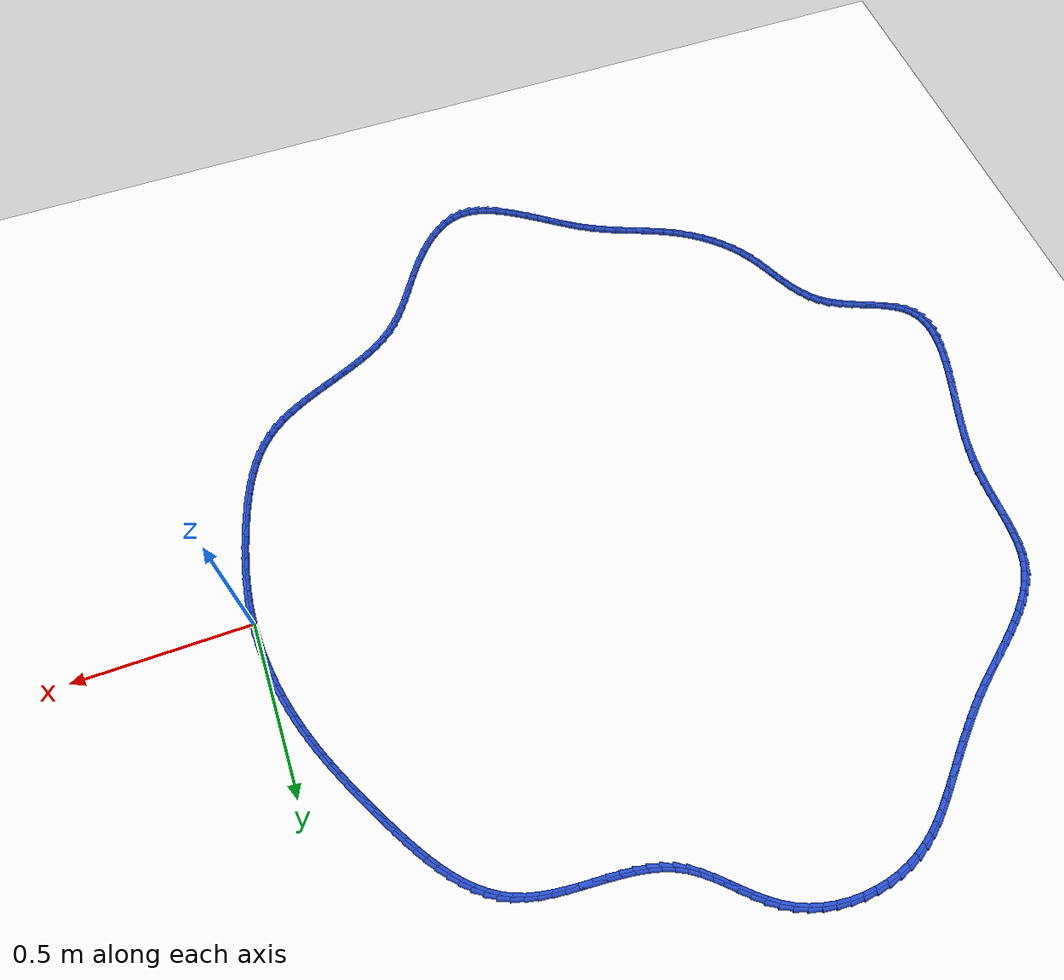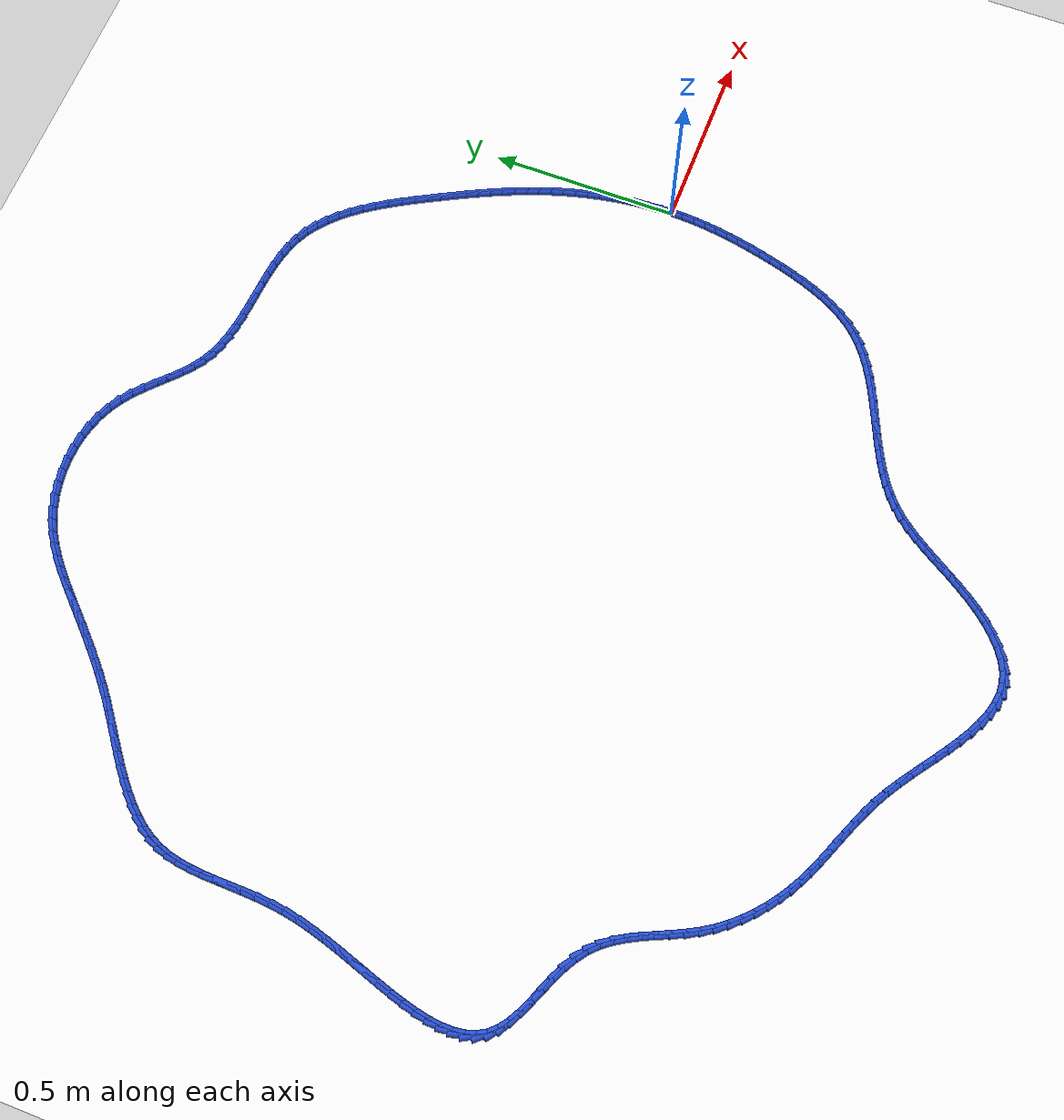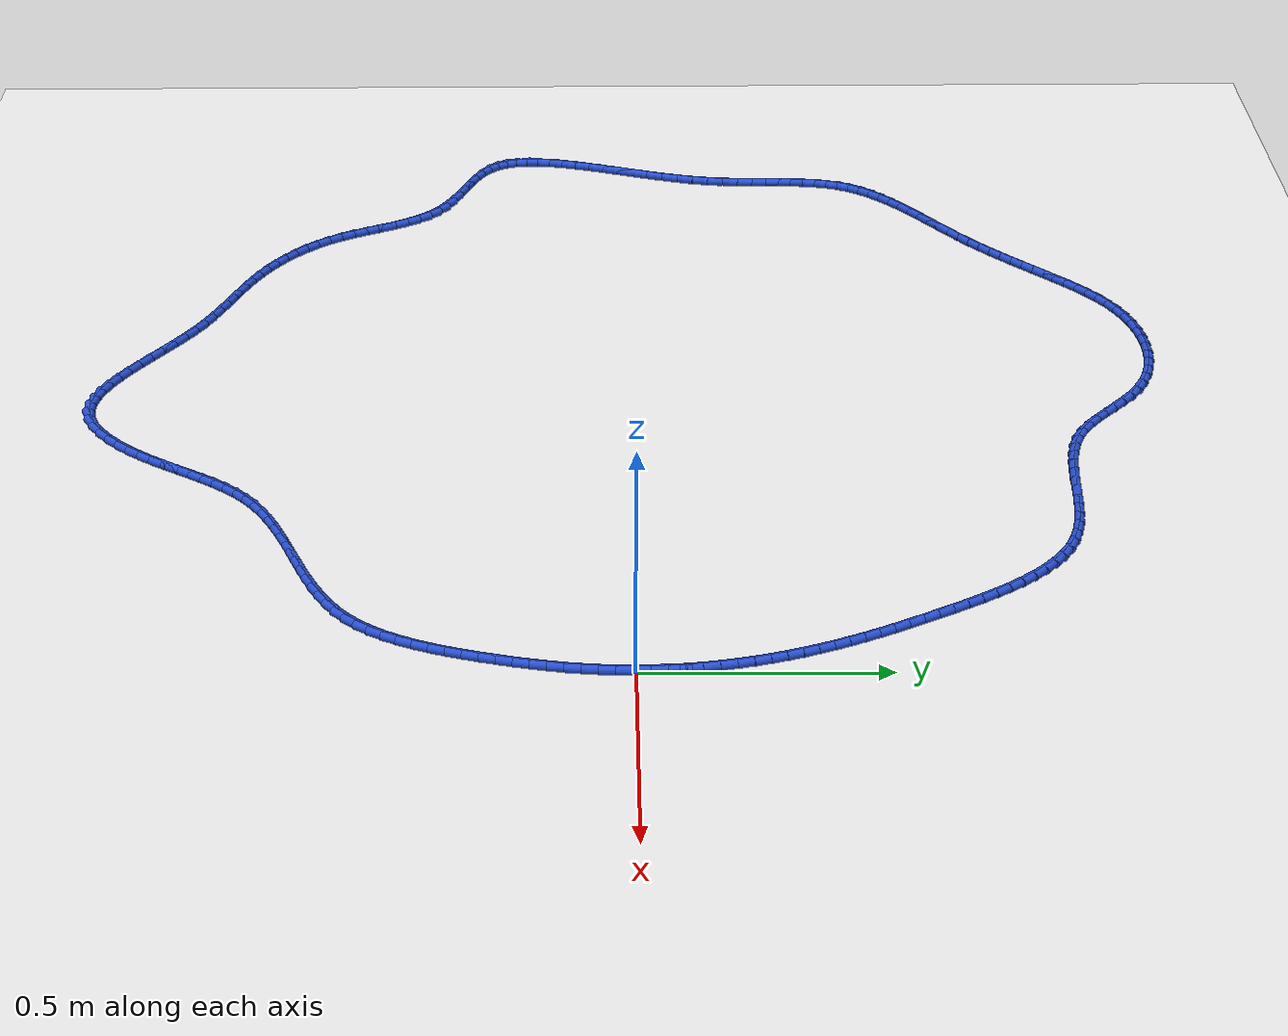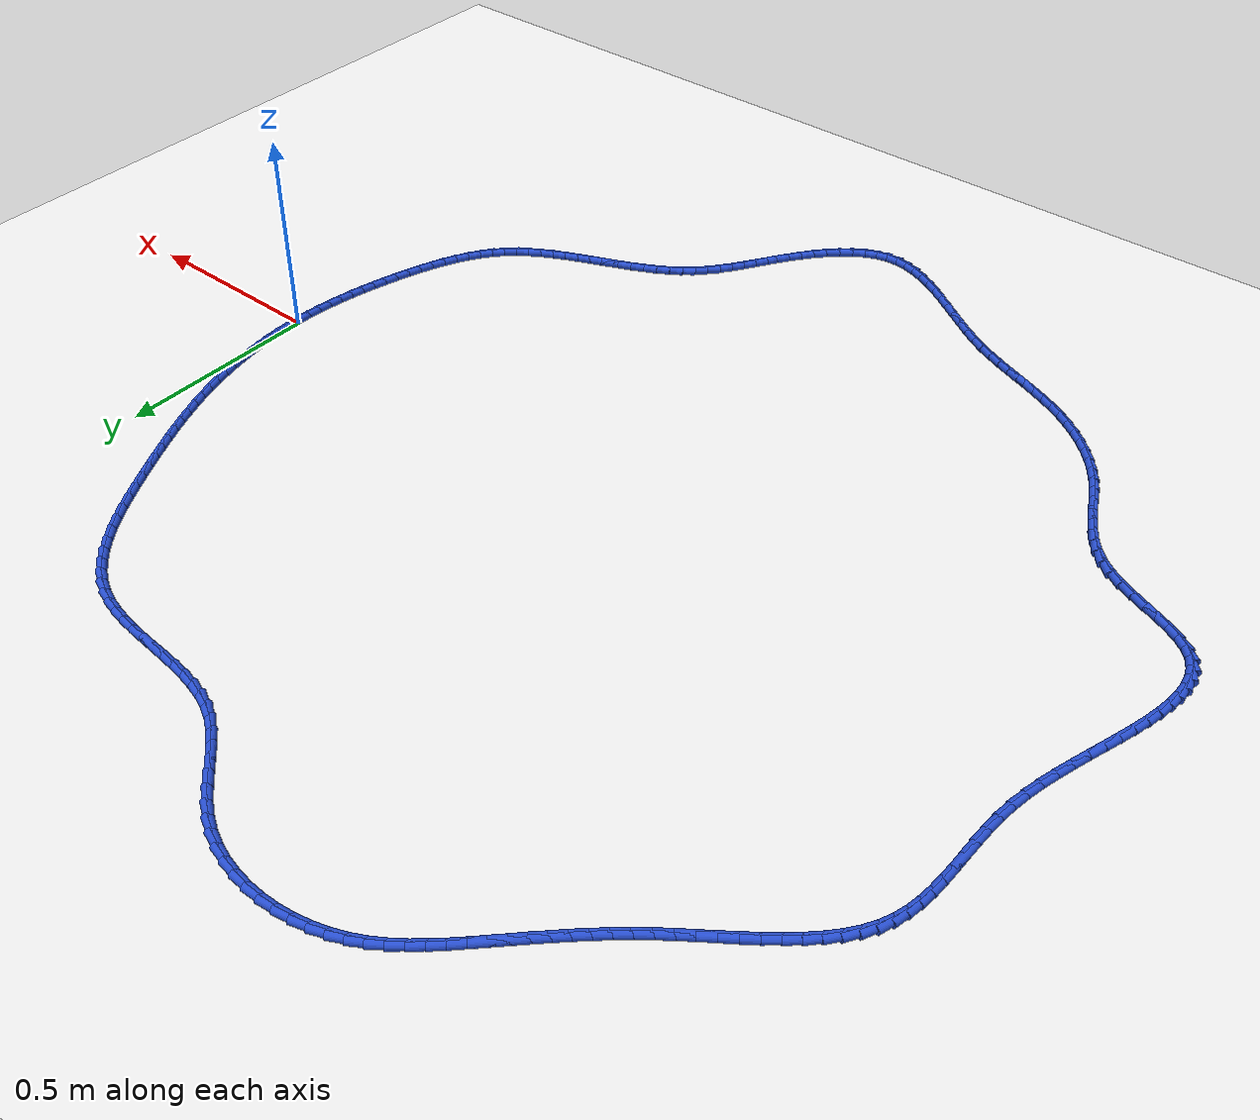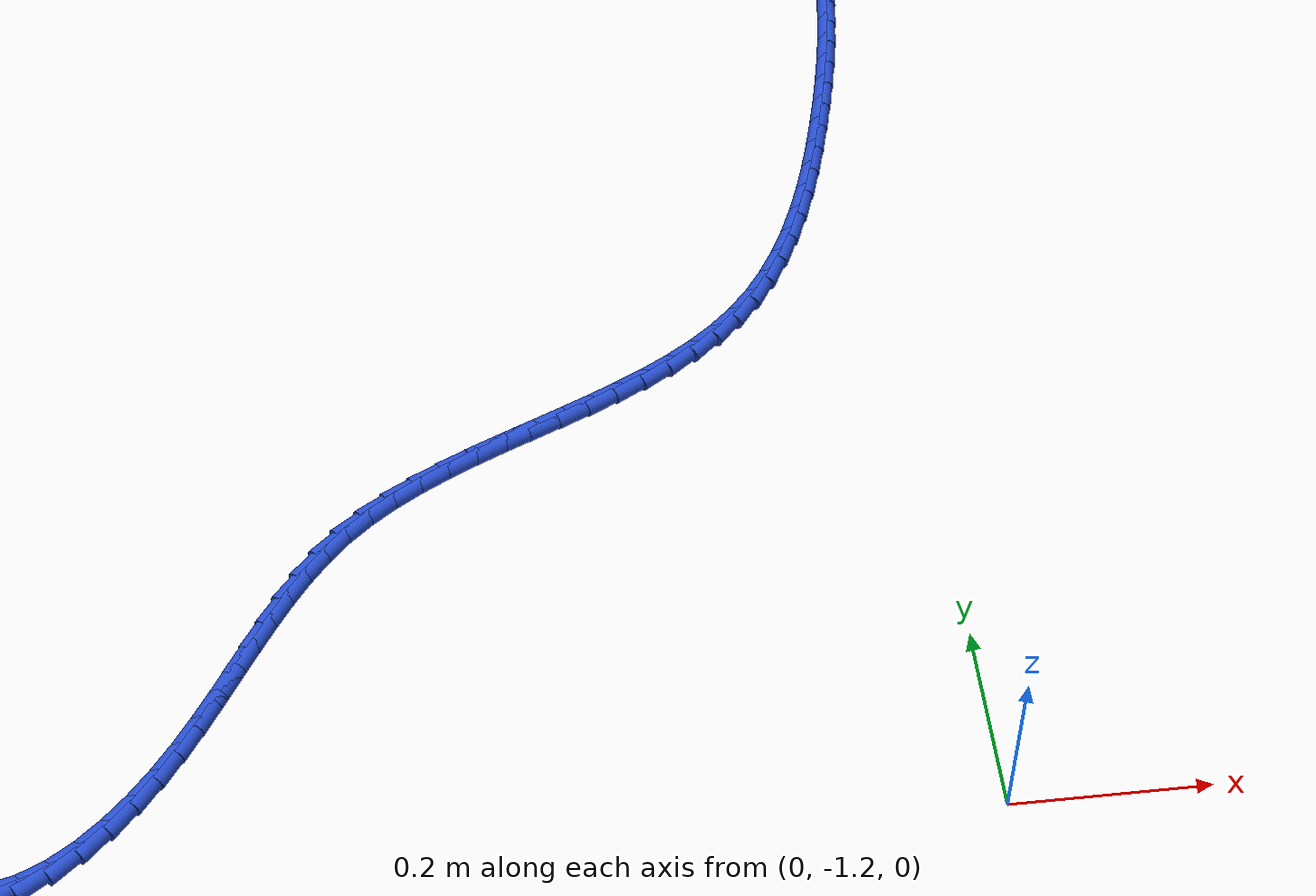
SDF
<sdf version="1.6">
 <world name="default">
  <light name="sun" type="directional">
   <pose>0 0 10 0 -0 0</pose>
   <diffuse>0.8 0.8 0.8 1</diffuse>
   <specular>0.2 0.2 0.2 1</specular>
   <attenuation>
    <range>1000</range>
    <constant>0.9</constant>
    <linear>0.01</linear>
    <quadratic>0.001</quadratic>
   </attenuation>
   <direction>-0.5 0.1 -0.9</direction>
  </light>
  <model name="ground_plane">
   <static>1</static>
   <link name="link">
    <collision name="collision">
     <geometry><plane><normal>0 0 1</normal><size>100 100</size></plane></geometry>
     <surface><friction><ode><mu>100</mu><mu2>50</mu2></ode></friction></surface>
    </collision>
    <visual name="visual">
     <cast_shadows>0</cast_shadows>
     <geometry><plane><normal>0 0 1</normal><size>100 100</size></plane></geometry>
     <material>
      <script><uri>file://media/materials/scripts/gazebo.material</uri><name>Gazebo/WhiteGlow</name></script>
     </material>
    </visual>
   </link>
  </model>
  <gravity>0 0 -9.8</gravity>
  <magnetic_field>6e-06 2.3e-05 -4.2e-05</magnetic_field>
  <atmosphere type="adiabatic"/>
  <physics name="default_physics" default="0" type="ode">
   <max_step_size>0.001</max_step_size>
   <real_time_factor>1</real_time_factor>
   <real_time_update_rate>1000</real_time_update_rate>
  </physics>
  <scene><ambient>0.4 0.4 0.4 1</ambient><background>0.7 0.7 0.7 1</background><shadows>1</shadows></scene>
  <spherical_coordinates>
   <surface_model>EARTH_WGS84</surface_model>
   <latitude_deg>0</latitude_deg>
   <longitude_deg>0</longitude_deg>
   <elevation>0</elevation>
   <heading_deg>0</heading_deg>
  </spherical_coordinates>
  <model name="line">
   <link name="link_0">
    <pose>-1.734723475976807e-18 -4.163336342344337e-17 0.01 0 1.57 -1.5573018915308656</pose>
    <collision name="collision">
     <geometry><cylinder><radius>0.01</radius><length>0.08</length></cylinder></geometry>
    </collision>
    <visual name="visual">
     <material>
      <script><name>Gazebo/Blue</name><uri>file://media/materials/scripts/gazebo.material</uri></script>
     </material>
     <geometry><cylinder><radius>0.01</radius><length>0.08</length></cylinder></geometry>
    </visual>
   </link>
   <link name="link_1">
    <pose>-0.0004494748009234489 0.033306137582674214 0.01 0 1.57 -1.5205700695620679</pose>
    <collision name="collision">
     <geometry><cylinder><radius>0.01</radius><length>0.08</length></cylinder></geometry>
    </collision>
    <visual name="visual">
     <material>
      <script><name>Gazebo/Blue</name><uri>file://media/materials/scripts/gazebo.material</uri></script>
     </material>
     <geometry><cylinder><radius>0.01</radius><length>0.08</length></cylinder></geometry>
    </visual>
   </link>
   <link name="link_2">
    <pose>-0.0021282769201872386 0.06670281657929593 0.01 0 1.57 -1.4851405836784912</pose>
    <collision name="collision">
     <geometry><cylinder><radius>0.01</radius><length>0.08</length></cylinder></geometry>
    </collision>
    <visual name="visual">
     <material>
      <script><name>Gazebo/Blue</name><uri>file://media/materials/scripts/gazebo.material</uri></script>
     </material>
     <geometry><cylinder><radius>0.01</radius><length>0.08</length></cylinder></geometry>
    </visual>
   </link>
   <link name="link_3">
    <pose>-0.00499719474859924 0.10011444740390042 0.01 0 1.57 -1.4508441671208696</pose>
    <collision name="collision">
     <geometry><cylinder><radius>0.01</radius><length>0.08</length></cylinder></geometry>
    </collision>
    <visual name="visual">
     <material>
      <script><name>Gazebo/Blue</name><uri>file://media/materials/scripts/gazebo.material</uri></script>
     </material>
     <geometry><cylinder><radius>0.01</radius><length>0.08</length></cylinder></geometry>
    </visual>
   </link>
   <link name="link_4">
    <pose>-0.009017016676967294 0.13346544047052303 0.01 0 1.57 -1.4175132402100814</pose>
    <collision name="collision">
     <geometry><cylinder><radius>0.01</radius><length>0.08</length></cylinder></geometry>
    </collision>
    <visual name="visual">
     <material>
      <script><name>Gazebo/Blue</name><uri>file://media/materials/scripts/gazebo.material</uri></script>
     </material>
     <geometry><cylinder><radius>0.01</radius><length>0.08</length></cylinder></geometry>
    </visual>
   </link>
   <link name="link_5">
    <pose>-0.014148531096099266 0.16668020619319907 0.01 0 1.57 -1.3849817635417208</pose>
    <collision name="collision">
     <geometry><cylinder><radius>0.01</radius><length>0.08</length></cylinder></geometry>
    </collision>
    <visual name="visual">
     <material>
      <script><name>Gazebo/Blue</name><uri>file://media/materials/scripts/gazebo.material</uri></script>
     </material>
     <geometry><cylinder><radius>0.01</radius><length>0.08</length></cylinder></geometry>
    </visual>
   </link>
   <link name="link_6">
    <pose>-0.020352526396803006 0.19968315498596392 0.01 0 1.57 -1.3530846146934308</pose>
    <collision name="collision">
     <geometry><cylinder><radius>0.01</radius><length>0.08</length></cylinder></geometry>
    </collision>
    <visual name="visual">
     <material>
      <script><name>Gazebo/Blue</name><uri>file://media/materials/scripts/gazebo.material</uri></script>
     </material>
     <geometry><cylinder><radius>0.01</radius><length>0.08</length></cylinder></geometry>
    </visual>
   </link>
   <link name="link_7">
    <pose>-0.027589790969886372 0.2323986972628528 0.01 0 1.57 -1.321656568100622</pose>
    <collision name="collision">
     <geometry><cylinder><radius>0.01</radius><length>0.08</length></cylinder></geometry>
    </collision>
    <visual name="visual">
     <material>
      <script><name>Gazebo/Blue</name><uri>file://media/materials/scripts/gazebo.material</uri></script>
     </material>
     <geometry><cylinder><radius>0.01</radius><length>0.08</length></cylinder></geometry>
    </visual>
   </link>
   <link name="link_8">
    <pose>-0.035821113206157204 0.26475124343790113 0.01 0 1.57 -1.2905309842531874</pose>
    <collision name="collision">
     <geometry><cylinder><radius>0.01</radius><length>0.08</length></cylinder></geometry>
    </collision>
    <visual name="visual">
     <material>
      <script><name>Gazebo/Blue</name><uri>file://media/materials/scripts/gazebo.material</uri></script>
     </material>
     <geometry><cylinder><radius>0.01</radius><length>0.08</length></cylinder></geometry>
    </visual>
   </link>
   <link name="link_9">
    <pose>-0.04500728123557899 0.29666520948381325 0.01 0 1.57 -1.2598593176932391</pose>
    <collision name="collision">
     <geometry><cylinder><radius>0.01</radius><length>0.08</length></cylinder></geometry>
    </collision>
    <visual name="visual">
     <material>
      <script><name>Gazebo/Blue</name><uri>file://media/materials/scripts/gazebo.material</uri></script>
     </material>
     <geometry><cylinder><radius>0.01</radius><length>0.08</length></cylinder></geometry>
    </visual>
   </link>
   <link name="link_10">
    <pose>-0.055107664901555574 0.32809523546798525 0.01 0 1.57 -1.2307163337002167</pose>
    <collision name="collision">
     <geometry><cylinder><radius>0.01</radius><length>0.08</length></cylinder></geometry>
    </collision>
    <visual name="visual">
     <material>
      <script><name>Gazebo/Blue</name><uri>file://media/materials/scripts/gazebo.material</uri></script>
     </material>
     <geometry><cylinder><radius>0.01</radius><length>0.08</length></cylinder></geometry>
    </visual>
   </link>
   <link name="link_11">
    <pose>-0.06607689624222901 0.3590969254512242 0.01 0 1.57 -1.2035299680736895</pose>
    <collision name="collision">
     <geometry><cylinder><radius>0.01</radius><length>0.08</length></cylinder></geometry>
    </collision>
    <visual name="visual">
     <material>
      <script><name>Gazebo/Blue</name><uri>file://media/materials/scripts/gazebo.material</uri></script>
     </material>
     <geometry><cylinder><radius>0.01</radius><length>0.08</length></cylinder></geometry>
    </visual>
   </link>
   <link name="link_12">
    <pose>-0.07786861917067017 0.38974694072393384 0.01 0 1.57 -1.1784873235248032</pose>
    <collision name="collision">
     <geometry><cylinder><radius>0.01</radius><length>0.08</length></cylinder></geometry>
    </collision>
    <visual name="visual">
     <material>
      <script><name>Gazebo/Blue</name><uri>file://media/materials/scripts/gazebo.material</uri></script>
     </material>
     <geometry><cylinder><radius>0.01</radius><length>0.08</length></cylinder></geometry>
    </visual>
   </link>
   <link name="link_13">
    <pose>-0.0904364775999499 0.42012194257651847 0.01 0 1.57 -1.1557367660093023</pose>
    <collision name="collision">
     <geometry><cylinder><radius>0.01</radius><length>0.08</length></cylinder></geometry>
    </collision>
    <visual name="visual">
     <material>
      <script><name>Gazebo/Blue</name><uri>file://media/materials/scripts/gazebo.material</uri></script>
     </material>
     <geometry><cylinder><radius>0.01</radius><length>0.08</length></cylinder></geometry>
    </visual>
   </link>
   <link name="link_14">
    <pose>-0.10373411544313907 0.45029859229938207 0.01 0 1.57 -1.1353880557767184</pose>
    <collision name="collision">
     <geometry><cylinder><radius>0.01</radius><length>0.08</length></cylinder></geometry>
    </collision>
    <visual name="visual">
     <material>
      <script><name>Gazebo/Blue</name><uri>file://media/materials/scripts/gazebo.material</uri></script>
     </material>
     <geometry><cylinder><radius>0.01</radius><length>0.08</length></cylinder></geometry>
    </visual>
   </link>
   <link name="link_15">
    <pose>-0.11771517661330848 0.48035355118292855 0.01 0 1.57 -1.1175140134919035</pose>
    <collision name="collision">
     <geometry><cylinder><radius>0.01</radius><length>0.08</length></cylinder></geometry>
    </collision>
    <visual name="visual">
     <material>
      <script><name>Gazebo/Blue</name><uri>file://media/materials/scripts/gazebo.material</uri></script>
     </material>
     <geometry><cylinder><radius>0.01</radius><length>0.08</length></cylinder></geometry>
    </visual>
   </link>
   <link name="link_16">
    <pose>-0.13233330502352905 0.5103634805175619 0.01 0 1.57 -1.1021532984503988</pose>
    <collision name="collision">
     <geometry><cylinder><radius>0.01</radius><length>0.08</length></cylinder></geometry>
    </collision>
    <visual name="visual">
     <material>
      <script><name>Gazebo/Blue</name><uri>file://media/materials/scripts/gazebo.material</uri></script>
     </material>
     <geometry><cylinder><radius>0.01</radius><length>0.08</length></cylinder></geometry>
    </visual>
   </link>
   <link name="link_17">
    <pose>-0.14754214458687157 0.5404050415936863 0.01 0 1.57 -1.0893138782590823</pose>
    <collision name="collision">
     <geometry><cylinder><radius>0.01</radius><length>0.08</length></cylinder></geometry>
    </collision>
    <visual name="visual">
     <material>
      <script><name>Gazebo/Blue</name><uri>file://media/materials/scripts/gazebo.material</uri></script>
     </material>
     <geometry><cylinder><radius>0.01</radius><length>0.08</length></cylinder></geometry>
    </visual>
   </link>
   <link name="link_18">
    <pose>-0.16329533921640693 0.5705548957017055 0.01 0 1.57 -1.0789768185840183</pose>
    <collision name="collision">
     <geometry><cylinder><radius>0.01</radius><length>0.08</length></cylinder></geometry>
    </collision>
    <visual name="visual">
     <material>
      <script><name>Gazebo/Blue</name><uri>file://media/materials/scripts/gazebo.material</uri></script>
     </material>
     <geometry><cylinder><radius>0.01</radius><length>0.08</length></cylinder></geometry>
    </visual>
   </link>
   <link name="link_19">
    <pose>-0.17954653282520597 0.6008897041320237 0.01 0 1.57 -1.0710127763693755</pose>
    <collision name="collision">
     <geometry><cylinder><radius>0.01</radius><length>0.08</length></cylinder></geometry>
    </collision>
    <visual name="visual">
     <material>
      <script><name>Gazebo/Blue</name><uri>file://media/materials/scripts/gazebo.material</uri></script>
     </material>
     <geometry><cylinder><radius>0.01</radius><length>0.08</length></cylinder></geometry>
    </visual>
   </link>
   <link name="link_20">
    <pose>-0.19625085571226797 0.6314824988389675 0.01 0 1.57 -1.0614453183892587</pose>
    <collision name="collision">
     <geometry><cylinder><radius>0.01</radius><length>0.08</length></cylinder></geometry>
    </collision>
    <visual name="visual">
     <material>
      <script><name>Gazebo/Blue</name><uri>file://media/materials/scripts/gazebo.material</uri></script>
     </material>
     <geometry><cylinder><radius>0.01</radius><length>0.08</length></cylinder></geometry>
    </visual>
   </link>
   <link name="link_21">
    <pose>-0.21343052859951442 0.6622424958474304 0.01 0 1.57 -1.0448038570359097</pose>
    <collision name="collision">
     <geometry><cylinder><radius>0.01</radius><length>0.08</length></cylinder></geometry>
    </collision>
    <visual name="visual">
     <material>
      <script><name>Gazebo/Blue</name><uri>file://media/materials/scripts/gazebo.material</uri></script>
     </material>
     <geometry><cylinder><radius>0.01</radius><length>0.08</length></cylinder></geometry>
    </visual>
   </link>
   <link name="link_22">
    <pose>-0.23120072769625538 0.6928519400454546 0.01 0 1.57 -1.0204761212976012</pose>
    <collision name="collision">
     <geometry><cylinder><radius>0.01</radius><length>0.08</length></cylinder></geometry>
    </collision>
    <visual name="visual">
     <material>
      <script><name>Gazebo/Blue</name><uri>file://media/materials/scripts/gazebo.material</uri></script>
     </material>
     <geometry><cylinder><radius>0.01</radius><length>0.08</length></cylinder></geometry>
    </visual>
   </link>
   <link name="link_23">
    <pose>-0.24968346165155633 0.7229763934262662 0.01 0 1.57 -0.9879949300519528</pose>
    <collision name="collision">
     <geometry><cylinder><radius>0.01</radius><length>0.08</length></cylinder></geometry>
    </collision>
    <visual name="visual">
     <material>
      <script><name>Gazebo/Blue</name><uri>file://media/materials/scripts/gazebo.material</uri></script>
     </material>
     <geometry><cylinder><radius>0.01</radius><length>0.08</length></cylinder></geometry>
    </visual>
   </link>
   <link name="link_24">
    <pose>-0.26900073911448275 0.7522814179830905 0.01 0 1.57 -0.9466564023853514</pose>
    <collision name="collision">
     <geometry><cylinder><radius>0.01</radius><length>0.08</length></cylinder></geometry>
    </collision>
    <visual name="visual">
     <material>
      <script><name>Gazebo/Blue</name><uri>file://media/materials/scripts/gazebo.material</uri></script>
     </material>
     <geometry><cylinder><radius>0.01</radius><length>0.08</length></cylinder></geometry>
    </visual>
   </link>
   <link name="link_25">
    <pose>-0.28927456873410007 0.7804325757091531 0.01 0 1.57 -0.8955499958110168</pose>
    <collision name="collision">
     <geometry><cylinder><radius>0.01</radius><length>0.08</length></cylinder></geometry>
    </collision>
    <visual name="visual">
     <material>
      <script><name>Gazebo/Blue</name><uri>file://media/materials/scripts/gazebo.material</uri></script>
     </material>
     <geometry><cylinder><radius>0.01</radius><length>0.08</length></cylinder></geometry>
    </visual>
   </link>
   <link name="link_26">
    <pose>-0.31062695915947364 0.80709542859768 0.01 0 1.57 -0.8336199201617173</pose>
    <collision name="collision">
     <geometry><cylinder><radius>0.01</radius><length>0.08</length></cylinder></geometry>
    </collision>
    <visual name="visual">
     <material>
      <script><name>Gazebo/Blue</name><uri>file://media/materials/scripts/gazebo.material</uri></script>
     </material>
     <geometry><cylinder><radius>0.01</radius><length>0.08</length></cylinder></geometry>
    </visual>
   </link>
   <link name="link_27">
    <pose>-0.3331799190396692 0.8319355386418968 0.01 0 1.57 -0.7597884703567064</pose>
    <collision name="collision">
     <geometry><cylinder><radius>0.01</radius><length>0.08</length></cylinder></geometry>
    </collision>
    <visual name="visual">
     <material>
      <script><name>Gazebo/Blue</name><uri>file://media/materials/scripts/gazebo.material</uri></script>
     </material>
     <geometry><cylinder><radius>0.01</radius><length>0.08</length></cylinder></geometry>
    </visual>
   </link>
   <link name="link_28">
    <pose>-0.35705545702375197 0.8546184678350291 0.01 0 1.57 -0.6731787419636209</pose>
    <collision name="collision">
     <geometry><cylinder><radius>0.01</radius><length>0.08</length></cylinder></geometry>
    </collision>
    <visual name="visual">
     <material>
      <script><name>Gazebo/Blue</name><uri>file://media/materials/scripts/gazebo.material</uri></script>
     </material>
     <geometry><cylinder><radius>0.01</radius><length>0.08</length></cylinder></geometry>
    </visual>
   </link>
   <link name="link_29">
    <pose>-0.3823755817607874 0.8748097781703029 0.01 0 1.57 -0.5734644982853306</pose>
    <collision name="collision">
     <geometry><cylinder><radius>0.01</radius><length>0.08</length></cylinder></geometry>
    </collision>
    <visual name="visual">
     <material>
      <script><name>Gazebo/Blue</name><uri>file://media/materials/scripts/gazebo.material</uri></script>
     </material>
     <geometry><cylinder><radius>0.01</radius><length>0.08</length></cylinder></geometry>
    </visual>
   </link>
   <link name="link_30">
    <pose>-0.4092623018998411 0.8921750316409433 0.01 0 1.57 -0.46133064306873806</pose>
    <collision name="collision">
     <geometry><cylinder><radius>0.01</radius><length>0.08</length></cylinder></geometry>
    </collision>
    <visual name="visual">
     <material>
      <script><name>Gazebo/Blue</name><uri>file://media/materials/scripts/gazebo.material</uri></script>
     </material>
     <geometry><cylinder><radius>0.01</radius><length>0.08</length></cylinder></geometry>
    </visual>
   </link>
   <link name="link_31">
    <pose>-0.4378375366721783 0.9063799848374091 0.01 0 1.57 -0.34584840475191103</pose>
    <collision name="collision">
     <geometry><cylinder><radius>0.01</radius><length>0.08</length></cylinder></geometry>
    </collision>
    <visual name="visual">
     <material>
      <script><name>Gazebo/Blue</name><uri>file://media/materials/scripts/gazebo.material</uri></script>
     </material>
     <geometry><cylinder><radius>0.01</radius><length>0.08</length></cylinder></geometry>
    </visual>
   </link>
   <link name="link_32">
    <pose>-0.46812918850703805 0.9172950002509768 0.01 0 1.57 -0.2493242789697999</pose>
    <collision name="collision">
     <geometry><cylinder><radius>0.01</radius><length>0.08</length></cylinder></geometry>
    </collision>
    <visual name="visual">
     <material>
      <script><name>Gazebo/Blue</name><uri>file://media/materials/scripts/gazebo.material</uri></script>
     </material>
     <geometry><cylinder><radius>0.01</radius><length>0.08</length></cylinder></geometry>
    </visual>
   </link>
   <link name="link_33">
    <pose>-0.49989298336568777 0.9253827697248059 0.01 0 1.57 -0.1751539922061514</pose>
    <collision name="collision">
     <geometry><cylinder><radius>0.01</radius><length>0.08</length></cylinder></geometry>
    </collision>
    <visual name="visual">
     <material>
      <script><name>Gazebo/Blue</name><uri>file://media/materials/scripts/gazebo.material</uri></script>
     </material>
     <geometry><cylinder><radius>0.01</radius><length>0.08</length></cylinder></geometry>
    </visual>
   </link>
   <link name="link_34">
    <pose>-0.5328356786993496 0.9312125537780104 0.01 0 1.57 -0.12180783175830326</pose>
    <collision name="collision">
     <geometry><cylinder><radius>0.01</radius><length>0.08</length></cylinder></geometry>
    </collision>
    <visual name="visual">
     <material>
      <script><name>Gazebo/Blue</name><uri>file://media/materials/scripts/gazebo.material</uri></script>
     </material>
     <geometry><cylinder><radius>0.01</radius><length>0.08</length></cylinder></geometry>
    </visual>
   </link>
   <link name="link_35">
    <pose>-0.5666640319592466 0.935353612929705 0.01 0 1.57 -0.08755960623708033</pose>
    <collision name="collision">
     <geometry><cylinder><radius>0.01</radius><length>0.08</length></cylinder></geometry>
    </collision>
    <visual name="visual">
     <material>
      <script><name>Gazebo/Blue</name><uri>file://media/materials/scripts/gazebo.material</uri></script>
     </material>
     <geometry><cylinder><radius>0.01</radius><length>0.08</length></cylinder></geometry>
    </visual>
   </link>
   <link name="link_36">
    <pose>-0.6010848005966006 0.9383752076990033 0.01 0 1.57 -0.07106088073360295</pose>
    <collision name="collision">
     <geometry><cylinder><radius>0.01</radius><length>0.08</length></cylinder></geometry>
    </collision>
    <visual name="visual">
     <material>
      <script><name>Gazebo/Blue</name><uri>file://media/materials/scripts/gazebo.material</uri></script>
     </material>
     <geometry><cylinder><radius>0.01</radius><length>0.08</length></cylinder></geometry>
    </visual>
   </link>
   <link name="link_37">
    <pose>-0.6358047420626347 0.9408465986050201 0.01 0 1.57 -0.07159477339910743</pose>
    <collision name="collision">
     <geometry><cylinder><radius>0.01</radius><length>0.08</length></cylinder></geometry>
    </collision>
    <visual name="visual">
     <material>
      <script><name>Gazebo/Blue</name><uri>file://media/materials/scripts/gazebo.material</uri></script>
     </material>
     <geometry><cylinder><radius>0.01</radius><length>0.08</length></cylinder></geometry>
    </visual>
   </link>
   <link name="link_38">
    <pose>-0.6705306138085708 0.943337046166869 0.01 0 1.57 -0.08916173959354533</pose>
    <collision name="collision">
     <geometry><cylinder><radius>0.01</radius><length>0.08</length></cylinder></geometry>
    </collision>
    <visual name="visual">
     <material>
      <script><name>Gazebo/Blue</name><uri>file://media/materials/scripts/gazebo.material</uri></script>
     </material>
     <geometry><cylinder><radius>0.01</radius><length>0.08</length></cylinder></geometry>
    </visual>
   </link>
   <link name="link_39">
    <pose>-0.7049691732856316 0.9464158109036644 0.01 0 1.57 -0.12447398670273596</pose>
    <collision name="collision">
     <geometry><cylinder><radius>0.01</radius><length>0.08</length></cylinder></geometry>
    </collision>
    <visual name="visual">
     <material>
      <script><name>Gazebo/Blue</name><uri>file://media/materials/scripts/gazebo.material</uri></script>
     </material>
     <geometry><cylinder><radius>0.01</radius><length>0.08</length></cylinder></geometry>
    </visual>
   </link>
   <link name="link_40">
    <pose>-0.7388271779450399 0.9506521533345211 0.01 0 1.57 -0.17885703616114024</pose>
    <collision name="collision">
     <geometry><cylinder><radius>0.01</radius><length>0.08</length></cylinder></geometry>
    </collision>
    <visual name="visual">
     <material>
      <script><name>Gazebo/Blue</name><uri>file://media/materials/scripts/gazebo.material</uri></script>
     </material>
     <geometry><cylinder><radius>0.01</radius><length>0.08</length></cylinder></geometry>
    </visual>
   </link>
   <link name="link_41">
    <pose>-0.7718113852380175 0.9566153339785525 0.01 0 1.57 -0.25397988530833004</pose>
    <collision name="collision">
     <geometry><cylinder><radius>0.01</radius><length>0.08</length></cylinder></geometry>
    </collision>
    <visual name="visual">
     <material>
      <script><name>Gazebo/Blue</name><uri>file://media/materials/scripts/gazebo.material</uri></script>
     </material>
     <geometry><cylinder><radius>0.01</radius><length>0.08</length></cylinder></geometry>
    </visual>
   </link>
   <link name="link_42">
    <pose>-0.8036285526157874 0.9648746133548729 0.01 0 1.57 -0.3512641926403313</pose>
    <collision name="collision">
     <geometry><cylinder><radius>0.01</radius><length>0.08</length></cylinder></geometry>
    </collision>
    <visual name="visual">
     <material>
      <script><name>Gazebo/Blue</name><uri>file://media/materials/scripts/gazebo.material</uri></script>
     </material>
     <geometry><cylinder><radius>0.01</radius><length>0.08</length></cylinder></geometry>
    </visual>
   </link>
   <link name="link_43">
    <pose>-0.8339854375295722 0.9759992519825973 0.01 0 1.57 -0.47070807525748876</pose>
    <collision name="collision">
     <geometry><cylinder><radius>0.01</radius><length>0.08</length></cylinder></geometry>
    </collision>
    <visual name="visual">
     <material>
      <script><name>Gazebo/Blue</name><uri>file://media/materials/scripts/gazebo.material</uri></script>
     </material>
     <geometry><cylinder><radius>0.01</radius><length>0.08</length></cylinder></geometry>
    </visual>
   </link>
   <link name="link_44">
    <pose>-0.8625906279466391 0.9905552032842995 0.01 0 1.57 -0.5932454401975124</pose>
    <collision name="collision">
     <geometry><cylinder><radius>0.01</radius><length>0.08</length></cylinder></geometry>
    </collision>
    <visual name="visual">
     <material>
      <script><name>Gazebo/Blue</name><uri>file://media/materials/scripts/gazebo.material</uri></script>
     </material>
     <geometry><cylinder><radius>0.01</radius><length>0.08</length></cylinder></geometry>
    </visual>
   </link>
   <link name="link_45">
    <pose>-0.8894120114027217 1.0086399578642238 0.01 0 1.57 -0.6827453569097348</pose>
    <collision name="collision">
     <geometry><cylinder><radius>0.01</radius><length>0.08</length></cylinder></geometry>
    </collision>
    <visual name="visual">
     <material>
      <script><name>Gazebo/Blue</name><uri>file://media/materials/scripts/gazebo.material</uri></script>
     </material>
     <geometry><cylinder><radius>0.01</radius><length>0.08</length></cylinder></geometry>
    </visual>
   </link>
   <link name="link_46">
    <pose>-0.9149428097183611 1.029401912654445 0.01 0 1.57 -0.7362705213759442</pose>
    <collision name="collision">
     <geometry><cylinder><radius>0.01</radius><length>0.08</length></cylinder></geometry>
    </collision>
    <visual name="visual">
     <material>
      <script><name>Gazebo/Blue</name><uri>file://media/materials/scripts/gazebo.material</uri></script>
     </material>
     <geometry><cylinder><radius>0.01</radius><length>0.08</length></cylinder></geometry>
    </visual>
   </link>
   <link name="link_47">
    <pose>-0.9397397506891532 1.0518747317001647 0.01 0 1.57 -0.756089096847041</pose>
    <collision name="collision">
     <geometry><cylinder><radius>0.01</radius><length>0.08</length></cylinder></geometry>
    </collision>
    <visual name="visual">
     <material>
      <script><name>Gazebo/Blue</name><uri>file://media/materials/scripts/gazebo.material</uri></script>
     </material>
     <geometry><cylinder><radius>0.01</radius><length>0.08</length></cylinder></geometry>
    </visual>
   </link>
   <link name="link_48">
    <pose>-0.9643595621106947 1.0750920790465845 0.01 0 1.57 -0.7436707142709178</pose>
    <collision name="collision">
     <geometry><cylinder><radius>0.01</radius><length>0.08</length></cylinder></geometry>
    </collision>
    <visual name="visual">
     <material>
      <script><name>Gazebo/Blue</name><uri>file://media/materials/scripts/gazebo.material</uri></script>
     </material>
     <geometry><cylinder><radius>0.01</radius><length>0.08</length></cylinder></geometry>
    </visual>
   </link>
   <link name="link_49">
    <pose>-0.9893589717785811 1.098087618738905 0.01 0 1.57 -0.699142902192928</pose>
    <collision name="collision">
     <geometry><cylinder><radius>0.01</radius><length>0.08</length></cylinder></geometry>
    </collision>
    <visual name="visual">
     <material>
      <script><name>Gazebo/Blue</name><uri>file://media/materials/scripts/gazebo.material</uri></script>
     </material>
     <geometry><cylinder><radius>0.01</radius><length>0.08</length></cylinder></geometry>
    </visual>
   </link>
   <link name="link_50">
    <pose>-1.0152947074884089 1.1198950148223283 0.01 0 1.57 -0.6217187157018607</pose>
    <collision name="collision">
     <geometry><cylinder><radius>0.01</radius><length>0.08</length></cylinder></geometry>
    </collision>
    <visual name="visual">
     <material>
      <script><name>Gazebo/Blue</name><uri>file://media/materials/scripts/gazebo.material</uri></script>
     </material>
     <geometry><cylinder><radius>0.01</radius><length>0.08</length></cylinder></geometry>
    </visual>
   </link>
   <link name="link_51">
    <pose>-1.0427234970357744 1.1395479313420562 0.01 0 1.57 -0.514019873171341</pose>
    <collision name="collision">
     <geometry><cylinder><radius>0.01</radius><length>0.08</length></cylinder></geometry>
    </collision>
    <visual name="visual">
     <material>
      <script><name>Gazebo/Blue</name><uri>file://media/materials/scripts/gazebo.material</uri></script>
     </material>
     <geometry><cylinder><radius>0.01</radius><length>0.08</length></cylinder></geometry>
    </visual>
   </link>
   <link name="link_52">
    <pose>-1.0721344591613655 1.1561547798654945 0.01 0 1.57 -0.40179190764381983</pose>
    <collision name="collision">
     <geometry><cylinder><radius>0.01</radius><length>0.08</length></cylinder></geometry>
    </collision>
    <visual name="visual">
     <material>
      <script><name>Gazebo/Blue</name><uri>file://media/materials/scripts/gazebo.material</uri></script>
     </material>
     <geometry><cylinder><radius>0.01</radius><length>0.08</length></cylinder></geometry>
    </visual>
   </link>
   <link name="link_53">
    <pose>-1.10344317014604 1.1694580716055827 0.01 0 1.57 -0.2973701814789746</pose>
    <collision name="collision">
     <geometry><cylinder><radius>0.01</radius><length>0.08</length></cylinder></geometry>
    </collision>
    <visual name="visual">
     <material>
      <script><name>Gazebo/Blue</name><uri>file://media/materials/scripts/gazebo.material</uri></script>
     </material>
     <geometry><cylinder><radius>0.01</radius><length>0.08</length></cylinder></geometry>
    </visual>
   </link>
   <link name="link_54">
    <pose>-1.13627609460566 1.1795199551467386 0.01 0 1.57 -0.19990667457121697</pose>
    <collision name="collision">
     <geometry><cylinder><radius>0.01</radius><length>0.08</length></cylinder></geometry>
    </collision>
    <visual name="visual">
     <material>
      <script><name>Gazebo/Blue</name><uri>file://media/materials/scripts/gazebo.material</uri></script>
     </material>
     <geometry><cylinder><radius>0.01</radius><length>0.08</length></cylinder></geometry>
    </visual>
   </link>
   <link name="link_55">
    <pose>-1.1702574868179003 1.186405022788991 0.01 0 1.57 -0.10813474050414479</pose>
    <collision name="collision">
     <geometry><cylinder><radius>0.01</radius><length>0.08</length></cylinder></geometry>
    </collision>
    <visual name="visual">
     <material>
      <script><name>Gazebo/Blue</name><uri>file://media/materials/scripts/gazebo.material</uri></script>
     </material>
     <geometry><cylinder><radius>0.01</radius><length>0.08</length></cylinder></geometry>
    </visual>
   </link>
   <link name="link_56">
    <pose>-1.2050116010604341 1.190177866832368 0.01 0 1.57 -0.02062837492942689</pose>
    <collision name="collision">
     <geometry><cylinder><radius>0.01</radius><length>0.08</length></cylinder></geometry>
    </collision>
    <visual name="visual">
     <material>
      <script><name>Gazebo/Blue</name><uri>file://media/materials/scripts/gazebo.material</uri></script>
     </material>
     <geometry><cylinder><radius>0.01</radius><length>0.08</length></cylinder></geometry>
    </visual>
   </link>
   <link name="link_57">
    <pose>-1.2401626916109363 1.1909030795768976 0.01 0 1.57 0.06410531051194077</pose>
    <collision name="collision">
     <geometry><cylinder><radius>0.01</radius><length>0.08</length></cylinder></geometry>
    </collision>
    <visual name="visual">
     <material>
      <script><name>Gazebo/Blue</name><uri>file://media/materials/scripts/gazebo.material</uri></script>
     </material>
     <geometry><cylinder><radius>0.01</radius><length>0.08</length></cylinder></geometry>
    </visual>
   </link>
   <link name="link_58">
    <pose>-1.275335012747081 1.1886452533226077 0.01 0 1.57 0.14758642458134646</pose>
    <collision name="collision">
     <geometry><cylinder><radius>0.01</radius><length>0.08</length></cylinder></geometry>
    </collision>
    <visual name="visual">
     <material>
      <script><name>Gazebo/Blue</name><uri>file://media/materials/scripts/gazebo.material</uri></script>
     </material>
     <geometry><cylinder><radius>0.01</radius><length>0.08</length></cylinder></geometry>
    </visual>
   </link>
   <link name="link_59">
    <pose>-1.310152818746542 1.183468980369527 0.01 0 1.57 0.23135551691995282</pose>
    <collision name="collision">
     <geometry><cylinder><radius>0.01</radius><length>0.08</length></cylinder></geometry>
    </collision>
    <visual name="visual">
     <material>
      <script><name>Gazebo/Blue</name><uri>file://media/materials/scripts/gazebo.material</uri></script>
     </material>
     <geometry><cylinder><radius>0.01</radius><length>0.08</length></cylinder></geometry>
    </visual>
   </link>
   <link name="link_60">
    <pose>-1.3442403638869937 1.1754388530176825 0.01 0 1.57 0.3169824499481687</pose>
    <collision name="collision">
     <geometry><cylinder><radius>0.01</radius><length>0.08</length></cylinder></geometry>
    </collision>
    <visual name="visual">
     <material>
      <script><name>Gazebo/Blue</name><uri>file://media/materials/scripts/gazebo.material</uri></script>
     </material>
     <geometry><cylinder><radius>0.01</radius><length>0.08</length></cylinder></geometry>
    </visual>
   </link>
   <link name="link_61">
    <pose>-1.3772219024461108 1.1646194635671039 0.01 0 1.57 0.40607531566782945</pose>
    <collision name="collision">
     <geometry><cylinder><radius>0.01</radius><length>0.08</length></cylinder></geometry>
    </collision>
    <visual name="visual">
     <material>
      <script><name>Gazebo/Blue</name><uri>file://media/materials/scripts/gazebo.material</uri></script>
     </material>
     <geometry><cylinder><radius>0.01</radius><length>0.08</length></cylinder></geometry>
    </visual>
   </link>
   <link name="link_62">
    <pose>-1.408721688701566 1.1510754043178177 0.01 0 1.57 0.49833022943852795</pose>
    <collision name="collision">
     <geometry><cylinder><radius>0.01</radius><length>0.08</length></cylinder></geometry>
    </collision>
    <visual name="visual">
     <material>
      <script><name>Gazebo/Blue</name><uri>file://media/materials/scripts/gazebo.material</uri></script>
     </material>
     <geometry><cylinder><radius>0.01</radius><length>0.08</length></cylinder></geometry>
    </visual>
   </link>
   <link name="link_63">
    <pose>-1.438431282298904 1.134909334314007 0.01 0 1.57 0.5823239168019104</pose>
    <collision name="collision">
     <geometry><cylinder><radius>0.01</radius><length>0.08</length></cylinder></geometry>
    </collision>
    <visual name="visual">
     <material>
      <script><name>Gazebo/Blue</name><uri>file://media/materials/scripts/gazebo.material</uri></script>
     </material>
     <geometry><cylinder><radius>0.01</radius><length>0.08</length></cylinder></geometry>
    </visual>
   </link>
   <link name="link_64">
    <pose>-1.4664537716423394 1.1164566661002735 0.01 0 1.57 0.6523564934999107</pose>
    <collision name="collision">
     <geometry><cylinder><radius>0.01</radius><length>0.08</length></cylinder></geometry>
    </collision>
    <visual name="visual">
     <material>
      <script><name>Gazebo/Blue</name><uri>file://media/materials/scripts/gazebo.material</uri></script>
     </material>
     <geometry><cylinder><radius>0.01</radius><length>0.08</length></cylinder></geometry>
    </visual>
   </link>
   <link name="link_65">
    <pose>-1.4930477354789766 1.096140754851777 0.01 0 1.57 0.7077951934457127</pose>
    <collision name="collision">
     <geometry><cylinder><radius>0.01</radius><length>0.08</length></cylinder></geometry>
    </collision>
    <visual name="visual">
     <material>
      <script><name>Gazebo/Blue</name><uri>file://media/materials/scripts/gazebo.material</uri></script>
     </material>
     <geometry><cylinder><radius>0.01</radius><length>0.08</length></cylinder></geometry>
    </visual>
   </link>
   <link name="link_66">
    <pose>-1.518472041981991 1.0743851194380254 0.01 0 1.57 0.7485814889560467</pose>
    <collision name="collision">
     <geometry><cylinder><radius>0.01</radius><length>0.08</length></cylinder></geometry>
    </collision>
    <visual name="visual">
     <material>
      <script><name>Gazebo/Blue</name><uri>file://media/materials/scripts/gazebo.material</uri></script>
     </material>
     <geometry><cylinder><radius>0.01</radius><length>0.08</length></cylinder></geometry>
    </visual>
   </link>
   <link name="link_67">
    <pose>-1.5429855593245583 1.0516132787285262 0.01 0 1.57 0.7748732498835863</pose>
    <collision name="collision">
     <geometry><cylinder><radius>0.01</radius><length>0.08</length></cylinder></geometry>
    </collision>
    <visual name="visual">
     <material>
      <script><name>Gazebo/Blue</name><uri>file://media/materials/scripts/gazebo.material</uri></script>
     </material>
     <geometry><cylinder><radius>0.01</radius><length>0.08</length></cylinder></geometry>
    </visual>
   </link>
   <link name="link_68">
    <pose>-1.566847155679854 1.028248751592787 0.01 0 1.57 0.7869054991160199</pose>
    <collision name="collision">
     <geometry><cylinder><radius>0.01</radius><length>0.08</length></cylinder></geometry>
    </collision>
    <visual name="visual">
     <material>
      <script><name>Gazebo/Blue</name><uri>file://media/materials/scripts/gazebo.material</uri></script>
     </material>
     <geometry><cylinder><radius>0.01</radius><length>0.08</length></cylinder></geometry>
    </visual>
   </link>
   <link name="link_69">
    <pose>-1.5903145943456718 1.0047104594562921 0.01 0 1.57 0.7889601581840595</pose>
    <collision name="collision">
     <geometry><cylinder><radius>0.01</radius><length>0.08</length></cylinder></geometry>
    </collision>
    <visual name="visual">
     <material>
      <script><name>Gazebo/Blue</name><uri>file://media/materials/scripts/gazebo.material</uri></script>
     </material>
     <geometry><cylinder><radius>0.01</radius><length>0.08</length></cylinder></geometry>
    </visual>
   </link>
   <link name="link_70">
    <pose>-1.6136060284112455 0.9812525036032852 0.01 0 1.57 0.786383488912937</pose>
    <collision name="collision">
     <geometry><cylinder><radius>0.01</radius><length>0.08</length></cylinder></geometry>
    </collision>
    <visual name="visual">
     <material>
      <script><name>Gazebo/Blue</name><uri>file://media/materials/scripts/gazebo.material</uri></script>
     </material>
     <geometry><cylinder><radius>0.01</radius><length>0.08</length></cylinder></geometry>
    </visual>
   </link>
   <link name="link_71">
    <pose>-1.6368900098113632 0.9579225923304766 0.01 0 1.57 0.77950360853138</pose>
    <collision name="collision">
     <geometry><cylinder><radius>0.01</radius><length>0.08</length></cylinder></geometry>
    </collision>
    <visual name="visual">
     <material>
      <script><name>Gazebo/Blue</name><uri>file://media/materials/scripts/gazebo.material</uri></script>
     </material>
     <geometry><cylinder><radius>0.01</radius><length>0.08</length></cylinder></geometry>
    </visual>
   </link>
   <link name="link_72">
    <pose>-1.660331955672457 0.9347553898337037 0.01 0 1.57 0.7683784043462404</pose>
    <collision name="collision">
     <geometry><cylinder><radius>0.01</radius><length>0.08</length></cylinder></geometry>
    </collision>
    <visual name="visual">
     <material>
      <script><name>Gazebo/Blue</name><uri>file://media/materials/scripts/gazebo.material</uri></script>
     </material>
     <geometry><cylinder><radius>0.01</radius><length>0.08</length></cylinder></geometry>
    </visual>
   </link>
   <link name="link_73">
    <pose>-1.6840972831209589 0.9117855603088035 0.01 0 1.57 0.7531413860307464</pose>
    <collision name="collision">
     <geometry><cylinder><radius>0.01</radius><length>0.08</length></cylinder></geometry>
    </collision>
    <visual name="visual">
     <material>
      <script><name>Gazebo/Blue</name><uri>file://media/materials/scripts/gazebo.material</uri></script>
     </material>
     <geometry><cylinder><radius>0.01</radius><length>0.08</length></cylinder></geometry>
    </visual>
   </link>
   <link name="link_74">
    <pose>-1.7083514092833008 0.8890477679516143 0.01 0 1.57 0.7340023476778366</pose>
    <collision name="collision">
     <geometry><cylinder><radius>0.01</radius><length>0.08</length></cylinder></geometry>
    </collision>
    <visual name="visual">
     <material>
      <script><name>Gazebo/Blue</name><uri>file://media/materials/scripts/gazebo.material</uri></script>
     </material>
     <geometry><cylinder><radius>0.01</radius><length>0.08</length></cylinder></geometry>
    </visual>
   </link>
   <link name="link_75">
    <pose>-1.7332597512859147 0.8665766769579729 0.01 0 1.57 0.7112458480106252</pose>
    <collision name="collision">
     <geometry><cylinder><radius>0.01</radius><length>0.08</length></cylinder></geometry>
    </collision>
    <visual name="visual">
     <material>
      <script><name>Gazebo/Blue</name><uri>file://media/materials/scripts/gazebo.material</uri></script>
     </material>
     <geometry><cylinder><radius>0.01</radius><length>0.08</length></cylinder></geometry>
    </visual>
   </link>
   <link name="link_76">
    <pose>-1.7589877262552323 0.8444069515237166 0.01 0 1.57 0.6852523705501307</pose>
    <collision name="collision">
     <geometry><cylinder><radius>0.01</radius><length>0.08</length></cylinder></geometry>
    </collision>
    <visual name="visual">
     <material>
      <script><name>Gazebo/Blue</name><uri>file://media/materials/scripts/gazebo.material</uri></script>
     </material>
     <geometry><cylinder><radius>0.01</radius><length>0.08</length></cylinder></geometry>
    </visual>
   </link>
   <link name="link_77">
    <pose>-1.7856997364363711 0.8225729395728273 0.01 0 1.57 0.6605381469614446</pose>
    <collision name="collision">
     <geometry><cylinder><radius>0.01</radius><length>0.08</length></cylinder></geometry>
    </collision>
    <visual name="visual">
     <material>
      <script><name>Gazebo/Blue</name><uri>file://media/materials/scripts/gazebo.material</uri></script>
     </material>
     <geometry><cylinder><radius>0.01</radius><length>0.08</length></cylinder></geometry>
    </visual>
   </link>
   <link name="link_78">
    <pose>-1.8133923415653759 0.8010566835419237 0.01 0 1.57 0.6455203686303415</pose>
    <collision name="collision">
     <geometry><cylinder><radius>0.01</radius><length>0.08</length></cylinder></geometry>
    </collision>
    <visual name="visual">
     <material>
      <script><name>Gazebo/Blue</name><uri>file://media/materials/scripts/gazebo.material</uri></script>
     </material>
     <geometry><cylinder><radius>0.01</radius><length>0.08</length></cylinder></geometry>
    </visual>
   </link>
   <link name="link_79">
    <pose>-1.8417085539267526 0.7797300483454884 0.01 0 1.57 0.6407040246989433</pose>
    <collision name="collision">
     <geometry><cylinder><radius>0.01</radius><length>0.08</length></cylinder></geometry>
    </collision>
    <visual name="visual">
     <material>
      <script><name>Gazebo/Blue</name><uri>file://media/materials/scripts/gazebo.material</uri></script>
     </material>
     <geometry><cylinder><radius>0.01</radius><length>0.08</length></cylinder></geometry>
    </visual>
   </link>
   <link name="link_80">
    <pose>-1.870246632952902 0.7584509523730555 0.01 0 1.57 0.6458662366305488</pose>
    <collision name="collision">
     <geometry><cylinder><radius>0.01</radius><length>0.08</length></cylinder></geometry>
    </collision>
    <visual name="visual">
     <material>
      <script><name>Gazebo/Blue</name><uri>file://media/materials/scripts/gazebo.material</uri></script>
     </material>
     <geometry><cylinder><radius>0.01</radius><length>0.08</length></cylinder></geometry>
    </visual>
   </link>
   <link name="link_81">
    <pose>-1.8986048380762228 0.7370773140141579 0.01 0 1.57 0.6611832936335186</pose>
    <collision name="collision">
     <geometry><cylinder><radius>0.01</radius><length>0.08</length></cylinder></geometry>
    </collision>
    <visual name="visual">
     <material>
      <script><name>Gazebo/Blue</name><uri>file://media/materials/scripts/gazebo.material</uri></script>
     </material>
     <geometry><cylinder><radius>0.01</radius><length>0.08</length></cylinder></geometry>
    </visual>
   </link>
   <link name="link_82">
    <pose>-1.9263814287291163 0.7154670516583294 0.01 0 1.57 0.6872307025824317</pose>
    <collision name="collision">
     <geometry><cylinder><radius>0.01</radius><length>0.08</length></cylinder></geometry>
    </collision>
    <visual name="visual">
     <material>
      <script><name>Gazebo/Blue</name><uri>file://media/materials/scripts/gazebo.material</uri></script>
     </material>
     <geometry><cylinder><radius>0.01</radius><length>0.08</length></cylinder></geometry>
    </visual>
   </link>
   <link name="link_83">
    <pose>-1.953174664343982 0.6934780836951038 0.01 0 1.57 0.7249852870610742</pose>
    <collision name="collision">
     <geometry><cylinder><radius>0.01</radius><length>0.08</length></cylinder></geometry>
    </collision>
    <visual name="visual">
     <material>
      <script><name>Gazebo/Blue</name><uri>file://media/materials/scripts/gazebo.material</uri></script>
     </material>
     <geometry><cylinder><radius>0.01</radius><length>0.08</length></cylinder></geometry>
    </visual>
   </link>
   <link name="link_84">
    <pose>-1.9785828043532188 0.6709683285140141 0.01 0 1.57 0.7758100373778083</pose>
    <collision name="collision">
     <geometry><cylinder><radius>0.01</radius><length>0.08</length></cylinder></geometry>
    </collision>
    <visual name="visual">
     <material>
      <script><name>Gazebo/Blue</name><uri>file://media/materials/scripts/gazebo.material</uri></script>
     </material>
     <geometry><cylinder><radius>0.01</radius><length>0.08</length></cylinder></geometry>
    </visual>
   </link>
   <link name="link_85">
    <pose>-2.0022041081892277 0.647795704504594 0.01 0 1.57 0.84138079612605</pose>
    <collision name="collision">
     <geometry><cylinder><radius>0.01</radius><length>0.08</length></cylinder></geometry>
    </collision>
    <visual name="visual">
     <material>
      <script><name>Gazebo/Blue</name><uri>file://media/materials/scripts/gazebo.material</uri></script>
     </material>
     <geometry><cylinder><radius>0.01</radius><length>0.08</length></cylinder></geometry>
    </visual>
   </link>
   <link name="link_86">
    <pose>-2.023636835284408 0.6238181300563774 0.01 0 1.57 0.9234813964851993</pose>
    <collision name="collision">
     <geometry><cylinder><radius>0.01</radius><length>0.08</length></cylinder></geometry>
    </collision>
    <visual name="visual">
     <material>
      <script><name>Gazebo/Blue</name><uri>file://media/materials/scripts/gazebo.material</uri></script>
     </material>
     <geometry><cylinder><radius>0.01</radius><length>0.08</length></cylinder></geometry>
    </visual>
   </link>
   <link name="link_87">
    <pose>-2.042479245071161 0.5988935235588977 0.01 0 1.57 1.0235612501364606</pose>
    <collision name="collision">
     <geometry><cylinder><radius>0.01</radius><length>0.08</length></cylinder></geometry>
    </collision>
    <visual name="visual">
     <material>
      <script><name>Gazebo/Blue</name><uri>file://media/materials/scripts/gazebo.material</uri></script>
     </material>
     <geometry><cylinder><radius>0.01</radius><length>0.08</length></cylinder></geometry>
    </visual>
   </link>
   <link name="link_88">
    <pose>-2.058329596981885 0.572879803401688 0.01 0 1.57 1.141622706556608</pose>
    <collision name="collision">
     <geometry><cylinder><radius>0.01</radius><length>0.08</length></cylinder></geometry>
    </collision>
    <visual name="visual">
     <material>
      <script><name>Gazebo/Blue</name><uri>file://media/materials/scripts/gazebo.material</uri></script>
     </material>
     <geometry><cylinder><radius>0.01</radius><length>0.08</length></cylinder></geometry>
    </visual>
   </link>
   <link name="link_89">
    <pose>-2.0707964439941233 0.5456370820991376 0.01 0 1.57 1.2621249616050907</pose>
    <collision name="collision">
     <geometry><cylinder><radius>0.01</radius><length>0.08</length></cylinder></geometry>
    </collision>
    <visual name="visual">
     <material>
      <script><name>Gazebo/Blue</name><uri>file://media/materials/scripts/gazebo.material</uri></script>
     </material>
     <geometry><cylinder><radius>0.01</radius><length>0.08</length></cylinder></geometry>
    </visual>
   </link>
   <link name="link_90">
    <pose>-2.079892184102288 0.5171115539165557 0.01 0 1.57 1.3632791009786671</pose>
    <collision name="collision">
     <geometry><cylinder><radius>0.01</radius><length>0.08</length></cylinder></geometry>
    </collision>
    <visual name="visual">
     <material>
      <script><name>Gazebo/Blue</name><uri>file://media/materials/scripts/gazebo.material</uri></script>
     </material>
     <geometry><cylinder><radius>0.01</radius><length>0.08</length></cylinder></geometry>
    </visual>
   </link>
   <link name="link_91">
    <pose>-2.086155965197611 0.48736169271048596 0.01 0 1.57 1.4418927126917094</pose>
    <collision name="collision">
     <geometry><cylinder><radius>0.01</radius><length>0.08</length></cylinder></geometry>
    </collision>
    <visual name="visual">
     <material>
      <script><name>Gazebo/Blue</name><uri>file://media/materials/scripts/gazebo.material</uri></script>
     </material>
     <geometry><cylinder><radius>0.01</radius><length>0.08</length></cylinder></geometry>
    </visual>
   </link>
   <link name="link_92">
    <pose>-2.0901623549415267 0.45645352225317914 0.01 0 1.57 1.498313127249006</pose>
    <collision name="collision">
     <geometry><cylinder><radius>0.01</radius><length>0.08</length></cylinder></geometry>
    </collision>
    <visual name="visual">
     <material>
      <script><name>Gazebo/Blue</name><uri>file://media/materials/scripts/gazebo.material</uri></script>
     </material>
     <geometry><cylinder><radius>0.01</radius><length>0.08</length></cylinder></geometry>
    </visual>
   </link>
   <link name="link_93">
    <pose>-2.092485920995472 0.4244530663168874 0.01 0 1.57 1.5340151382224891</pose>
    <collision name="collision">
     <geometry><cylinder><radius>0.01</radius><length>0.08</length></cylinder></geometry>
    </collision>
    <visual name="visual">
     <material>
      <script><name>Gazebo/Blue</name><uri>file://media/materials/scripts/gazebo.material</uri></script>
     </material>
     <geometry><cylinder><radius>0.01</radius><length>0.08</length></cylinder></geometry>
    </visual>
   </link>
   <link name="link_94">
    <pose>-2.0937012310208813 0.3914263486738614 0.01 0 1.57 1.550743624757005</pose>
    <collision name="collision">
     <geometry><cylinder><radius>0.01</radius><length>0.08</length></cylinder></geometry>
    </collision>
    <visual name="visual">
     <material>
      <script><name>Gazebo/Blue</name><uri>file://media/materials/scripts/gazebo.material</uri></script>
     </material>
     <geometry><cylinder><radius>0.01</radius><length>0.08</length></cylinder></geometry>
    </visual>
   </link>
   <link name="link_95">
    <pose>-2.0943828526791917 0.3574393930963523 0.01 0 1.57 1.5500860794587448</pose>
    <collision name="collision">
     <geometry><cylinder><radius>0.01</radius><length>0.08</length></cylinder></geometry>
    </collision>
    <visual name="visual">
     <material>
      <script><name>Gazebo/Blue</name><uri>file://media/materials/scripts/gazebo.material</uri></script>
     </material>
     <geometry><cylinder><radius>0.01</radius><length>0.08</length></cylinder></geometry>
    </visual>
   </link>
   <link name="link_96">
    <pose>-2.0951053536318374 0.3225582233566119 0.01 0 1.57 1.53334613595057</pose>
    <collision name="collision">
     <geometry><cylinder><radius>0.01</radius><length>0.08</length></cylinder></geometry>
    </collision>
    <visual name="visual">
     <material>
      <script><name>Gazebo/Blue</name><uri>file://media/materials/scripts/gazebo.material</uri></script>
     </material>
     <geometry><cylinder><radius>0.01</radius><length>0.08</length></cylinder></geometry>
    </visual>
   </link>
   <link name="link_97">
    <pose>-2.096443301540254 0.28684886322689085 0.01 0 1.57 1.501593691564026</pose>
    <collision name="collision">
     <geometry><cylinder><radius>0.01</radius><length>0.08</length></cylinder></geometry>
    </collision>
    <visual name="visual">
     <material>
      <script><name>Gazebo/Blue</name><uri>file://media/materials/scripts/gazebo.material</uri></script>
     </material>
     <geometry><cylinder><radius>0.01</radius><length>0.08</length></cylinder></geometry>
    </visual>
   </link>
   <link name="link_98">
    <pose>-2.0989712640658773 0.2503773364794404 0.01 0 1.57 1.4558143780064379</pose>
    <collision name="collision">
     <geometry><cylinder><radius>0.01</radius><length>0.08</length></cylinder></geometry>
    </collision>
    <visual name="visual">
     <material>
      <script><name>Gazebo/Blue</name><uri>file://media/materials/scripts/gazebo.material</uri></script>
     </material>
     <geometry><cylinder><radius>0.01</radius><length>0.08</length></cylinder></geometry>
    </visual>
   </link>
   <link name="link_99">
    <pose>-2.1032638088701434 0.21320966688651233 0.01 0 1.57 1.3987699374190992</pose>
    <collision name="collision">
     <geometry><cylinder><radius>0.01</radius><length>0.08</length></cylinder></geometry>
    </collision>
    <visual name="visual">
     <material>
      <script><name>Gazebo/Blue</name><uri>file://media/materials/scripts/gazebo.material</uri></script>
     </material>
     <geometry><cylinder><radius>0.01</radius><length>0.08</length></cylinder></geometry>
    </visual>
   </link>
   <link name="link_100">
    <pose>-2.109829373528053 0.17542086333916065 0.01 0 1.57 1.3469061234210413</pose>
    <collision name="collision">
     <geometry><cylinder><radius>0.01</radius><length>0.08</length></cylinder></geometry>
    </collision>
    <visual name="visual">
     <material>
      <script><name>Gazebo/Blue</name><uri>file://media/materials/scripts/gazebo.material</uri></script>
     </material>
     <geometry><cylinder><radius>0.01</radius><length>0.08</length></cylinder></geometry>
    </visual>
   </link>
   <link name="link_101">
    <pose>-2.1185388070807027 0.1371725641135406 0.01 0 1.57 1.3077334688937876</pose>
    <collision name="collision">
     <geometry><cylinder><radius>0.01</radius><length>0.08</length></cylinder></geometry>
    </collision>
    <visual name="visual">
     <material>
      <script><name>Gazebo/Blue</name><uri>file://media/materials/scripts/gazebo.material</uri></script>
     </material>
     <geometry><cylinder><radius>0.01</radius><length>0.08</length></cylinder></geometry>
    </visual>
   </link>
   <link name="link_102">
    <pose>-2.128906387812486 0.0986748548837087 0.01 0 1.57 1.2799312138887364</pose>
    <collision name="collision">
     <geometry><cylinder><radius>0.01</radius><length>0.08</length></cylinder></geometry>
    </collision>
    <visual name="visual">
     <material>
      <script><name>Gazebo/Blue</name><uri>file://media/materials/scripts/gazebo.material</uri></script>
     </material>
     <geometry><cylinder><radius>0.01</radius><length>0.08</length></cylinder></geometry>
    </visual>
   </link>
   <link name="link_103">
    <pose>-2.1404424896846677 0.0601383518055184 0.01 0 1.57 1.2625529457720432</pose>
    <collision name="collision">
     <geometry><cylinder><radius>0.01</radius><length>0.08</length></cylinder></geometry>
    </collision>
    <visual name="visual">
     <material>
      <script><name>Gazebo/Blue</name><uri>file://media/materials/scripts/gazebo.material</uri></script>
     </material>
     <geometry><cylinder><radius>0.01</radius><length>0.08</length></cylinder></geometry>
    </visual>
   </link>
   <link name="link_104">
    <pose>-2.1526574866585095 0.021773671034823586 0.01 0 1.57 1.2551354331730136</pose>
    <collision name="collision">
     <geometry><cylinder><radius>0.01</radius><length>0.08</length></cylinder></geometry>
    </collision>
    <visual name="visual">
     <material>
      <script><name>Gazebo/Blue</name><uri>file://media/materials/scripts/gazebo.material</uri></script>
     </material>
     <geometry><cylinder><radius>0.01</radius><length>0.08</length></cylinder></geometry>
    </visual>
   </link>
   <link name="link_105">
    <pose>-2.1650617526952765 -0.01620857127252186 0.01 0 1.57 1.2577157711481741</pose>
    <collision name="collision">
     <geometry><cylinder><radius>0.01</radius><length>0.08</length></cylinder></geometry>
    </collision>
    <visual name="visual">
     <material>
      <script><name>Gazebo/Blue</name><uri>file://media/materials/scripts/gazebo.material</uri></script>
     </material>
     <geometry><cylinder><radius>0.01</radius><length>0.08</length></cylinder></geometry>
    </visual>
   </link>
   <link name="link_106">
    <pose>-2.177165661756231 -0.05359775896066492 0.01 0 1.57 1.2708786647966608</pose>
    <collision name="collision">
     <geometry><cylinder><radius>0.01</radius><length>0.08</length></cylinder></geometry>
    </collision>
    <visual name="visual">
     <material>
      <script><name>Gazebo/Blue</name><uri>file://media/materials/scripts/gazebo.material</uri></script>
     </material>
     <geometry><cylinder><radius>0.01</radius><length>0.08</length></cylinder></geometry>
    </visual>
   </link>
   <link name="link_107">
    <pose>-2.1884795878026386 -0.09018327587375 0.01 0 1.57 1.2958498728026093</pose>
    <collision name="collision">
     <geometry><cylinder><radius>0.01</radius><length>0.08</length></cylinder></geometry>
    </collision>
    <visual name="visual">
     <material>
      <script><name>Gazebo/Blue</name><uri>file://media/materials/scripts/gazebo.material</uri></script>
     </material>
     <geometry><cylinder><radius>0.01</radius><length>0.08</length></cylinder></geometry>
    </visual>
   </link>
   <link name="link_108">
    <pose>-2.19851390479576 -0.12575450585592413 0.01 0 1.57 1.3346467912752662</pose>
    <collision name="collision">
     <geometry><cylinder><radius>0.01</radius><length>0.08</length></cylinder></geometry>
    </collision>
    <visual name="visual">
     <material>
      <script><name>Gazebo/Blue</name><uri>file://media/materials/scripts/gazebo.material</uri></script>
     </material>
     <geometry><cylinder><radius>0.01</radius><length>0.08</length></cylinder></geometry>
    </visual>
   </link>
   <link name="link_109">
    <pose>-2.2067789866968606 -0.16010083275133333 0.01 0 1.57 1.3902829541110284</pose>
    <collision name="collision">
     <geometry><cylinder><radius>0.01</radius><length>0.08</length></cylinder></geometry>
    </collision>
    <visual name="visual">
     <material>
      <script><name>Gazebo/Blue</name><uri>file://media/materials/scripts/gazebo.material</uri></script>
     </material>
     <geometry><cylinder><radius>0.01</radius><length>0.08</length></cylinder></geometry>
    </visual>
   </link>
   <link name="link_110">
    <pose>-2.212785207467204 -0.19301164040412386 0.01 0 1.57 1.4669724426384836</pose>
    <collision name="collision">
     <geometry><cylinder><radius>0.01</radius><length>0.08</length></cylinder></geometry>
    </collision>
    <visual name="visual">
     <material>
      <script><name>Gazebo/Blue</name><uri>file://media/materials/scripts/gazebo.material</uri></script>
     </material>
     <geometry><cylinder><radius>0.01</radius><length>0.08</length></cylinder></geometry>
    </visual>
   </link>
   <link name="link_111">
    <pose>-2.2160429410680527 -0.2242763126584417 0.01 0 1.57 1.570129146346911</pose>
    <collision name="collision">
     <geometry><cylinder><radius>0.01</radius><length>0.08</length></cylinder></geometry>
    </collision>
    <visual name="visual">
     <material>
      <script><name>Gazebo/Blue</name><uri>file://media/materials/scripts/gazebo.material</uri></script>
     </material>
     <geometry><cylinder><radius>0.01</radius><length>0.08</length></cylinder></geometry>
    </visual>
   </link>
   <link name="link_112">
    <pose>-2.216062561460671 -0.2536842333584338 0.01 0 1.57 -1.435991812527895</pose>
    <collision name="collision">
     <geometry><cylinder><radius>0.01</radius><length>0.08</length></cylinder></geometry>
    </collision>
    <visual name="visual">
     <material>
      <script><name>Gazebo/Blue</name><uri>file://media/materials/scripts/gazebo.material</uri></script>
     </material>
     <geometry><cylinder><radius>0.01</radius><length>0.08</length></cylinder></geometry>
    </visual>
   </link>
   <link name="link_113">
    <pose>-2.2123544426063213 -0.28102478634824474 0.01 0 1.57 -1.2645188163280245</pose>
    <collision name="collision">
     <geometry><cylinder><radius>0.01</radius><length>0.08</length></cylinder></geometry>
    </collision>
    <visual name="visual">
     <material>
      <script><name>Gazebo/Blue</name><uri>file://media/materials/scripts/gazebo.material</uri></script>
     </material>
     <geometry><cylinder><radius>0.01</radius><length>0.08</length></cylinder></geometry>
    </visual>
   </link>
   <link name="link_114">
    <pose>-2.2044289584662686 -0.3060873554720215 0.01 0 1.57 -1.0606097852818104</pose>
    <collision name="collision">
     <geometry><cylinder><radius>0.01</radius><length>0.08</length></cylinder></geometry>
    </collision>
    <visual name="visual">
     <material>
      <script><name>Gazebo/Blue</name><uri>file://media/materials/scripts/gazebo.material</uri></script>
     </material>
     <geometry><cylinder><radius>0.01</radius><length>0.08</length></cylinder></geometry>
    </visual>
   </link>
   <link name="link_115">
    <pose>-2.1917964830017764 -0.32866132457391006 0.01 0 1.57 -0.8396185232319554</pose>
    <collision name="collision">
     <geometry><cylinder><radius>0.01</radius><length>0.08</length></cylinder></geometry>
    </collision>
    <visual name="visual">
     <material>
      <script><name>Gazebo/Blue</name><uri>file://media/materials/scripts/gazebo.material</uri></script>
     </material>
     <geometry><cylinder><radius>0.01</radius><length>0.08</length></cylinder></geometry>
    </visual>
   </link>
   <link name="link_116">
    <pose>-2.173967802128631 -0.3485363179047365 0.01 0 1.57 -0.6393928392126387</pose>
    <collision name="collision">
     <geometry><cylinder><radius>0.01</radius><length>0.08</length></cylinder></geometry>
    </collision>
    <visual name="visual">
     <material>
      <script><name>Gazebo/Blue</name><uri>file://media/materials/scripts/gazebo.material</uri></script>
     </material>
     <geometry><cylinder><radius>0.01</radius><length>0.08</length></cylinder></geometry>
    </visual>
   </link>
   <link name="link_117">
    <pose>-2.1508451005849127 -0.3657303705859582 0.01 0 1.57 -0.5061208700089077</pose>
    <collision name="collision">
     <geometry><cylinder><radius>0.01</radius><length>0.08</length></cylinder></geometry>
    </collision>
    <visual name="visual">
     <material>
      <script><name>Gazebo/Blue</name><uri>file://media/materials/scripts/gazebo.material</uri></script>
     </material>
     <geometry><cylinder><radius>0.01</radius><length>0.08</length></cylinder></geometry>
    </visual>
   </link>
   <link name="link_118">
    <pose>-2.123450041634043 -0.3809148182858456 0.01 0 1.57 -0.4299633692026011</pose>
    <collision name="collision">
     <geometry><cylinder><radius>0.01</radius><length>0.08</length></cylinder></geometry>
    </collision>
    <visual name="visual">
     <material>
      <script><name>Gazebo/Blue</name><uri>file://media/materials/scripts/gazebo.material</uri></script>
     </material>
     <geometry><cylinder><radius>0.01</radius><length>0.08</length></cylinder></geometry>
    </visual>
   </link>
   <link name="link_119">
    <pose>-2.093003155403199 -0.39487705055659356 0.01 0 1.57 -0.3968526791243273</pose>
    <collision name="collision">
     <geometry><cylinder><radius>0.01</radius><length>0.08</length></cylinder></geometry>
    </collision>
    <visual name="visual">
     <material>
      <script><name>Gazebo/Blue</name><uri>file://media/materials/scripts/gazebo.material</uri></script>
     </material>
     <geometry><cylinder><radius>0.01</radius><length>0.08</length></cylinder></geometry>
    </visual>
   </link>
   <link name="link_120">
    <pose>-2.0607249720195613 -0.40840445695039596 0.01 0 1.57 -0.39934837754821556</pose>
    <collision name="collision">
     <geometry><cylinder><radius>0.01</radius><length>0.08</length></cylinder></geometry>
    </collision>
    <visual name="visual">
     <material>
      <script><name>Gazebo/Blue</name><uri>file://media/materials/scripts/gazebo.material</uri></script>
     </material>
     <geometry><cylinder><radius>0.01</radius><length>0.08</length></cylinder></geometry>
    </visual>
   </link>
   <link name="link_121">
    <pose>-2.0278360216103053 -0.42228442701944763 0.01 0 1.57 -0.4355149400563301</pose>
    <collision name="collision">
     <geometry><cylinder><radius>0.01</radius><length>0.08</length></cylinder></geometry>
    </collision>
    <visual name="visual">
     <material>
      <script><name>Gazebo/Blue</name><uri>file://media/materials/scripts/gazebo.material</uri></script>
     </material>
     <geometry><cylinder><radius>0.01</radius><length>0.08</length></cylinder></geometry>
    </visual>
   </link>
   <link name="link_122">
    <pose>-1.9955568343026109 -0.4373043503159433 0.01 0 1.57 -0.5078815108859556</pose>
    <collision name="collision">
     <geometry><cylinder><radius>0.01</radius><length>0.08</length></cylinder></geometry>
    </collision>
    <visual name="visual">
     <material>
      <script><name>Gazebo/Blue</name><uri>file://media/materials/scripts/gazebo.material</uri></script>
     </material>
     <geometry><cylinder><radius>0.01</radius><length>0.08</length></cylinder></geometry>
    </visual>
   </link>
   <link name="link_123">
    <pose>-1.9651079402236558 -0.45425161639207734 0.01 0 1.57 -0.6224662837260744</pose>
    <collision name="collision">
     <geometry><cylinder><radius>0.01</radius><length>0.08</length></cylinder></geometry>
    </collision>
    <visual name="visual">
     <material>
      <script><name>Gazebo/Blue</name><uri>file://media/materials/scripts/gazebo.material</uri></script>
     </material>
     <geometry><cylinder><radius>0.01</radius><length>0.08</length></cylinder></geometry>
    </visual>
   </link>
   <link name="link_124">
    <pose>-1.9377098138607587 -0.47391357618367835 0.01 0 1.57 -0.7719172909889845</pose>
    <collision name="collision">
     <geometry><cylinder><radius>0.01</radius><length>0.08</length></cylinder></geometry>
    </collision>
    <visual name="visual">
     <material>
      <script><name>Gazebo/Blue</name><uri>file://media/materials/scripts/gazebo.material</uri></script>
     </material>
     <geometry><cylinder><radius>0.01</radius><length>0.08</length></cylinder></geometry>
    </visual>
   </link>
   <link name="link_125">
    <pose>-1.9141916679884465 -0.49680602879573327 0.01 0 1.57 -0.9065160102175781</pose>
    <collision name="collision">
     <geometry><cylinder><radius>0.01</radius><length>0.08</length></cylinder></geometry>
    </collision>
    <visual name="visual">
     <material>
      <script><name>Gazebo/Blue</name><uri>file://media/materials/scripts/gazebo.material</uri></script>
     </material>
     <geometry><cylinder><radius>0.01</radius><length>0.08</length></cylinder></geometry>
    </visual>
   </link>
   <link name="link_126">
    <pose>-1.8940552648370443 -0.5225234676857663 0.01 0 1.57 -1.0103827231081042</pose>
    <collision name="collision">
     <geometry><cylinder><radius>0.01</radius><length>0.08</length></cylinder></geometry>
    </collision>
    <visual name="visual">
     <material>
      <script><name>Gazebo/Blue</name><uri>file://media/materials/scripts/gazebo.material</uri></script>
     </material>
     <geometry><cylinder><radius>0.01</radius><length>0.08</length></cylinder></geometry>
    </visual>
   </link>
   <link name="link_127">
    <pose>-1.876521114274096 -0.5504651855248635 0.01 0 1.57 -1.0823350259223155</pose>
    <collision name="collision">
     <geometry><cylinder><radius>0.01</radius><length>0.08</length></cylinder></geometry>
    </collision>
    <visual name="visual">
     <material>
      <script><name>Gazebo/Blue</name><uri>file://media/materials/scripts/gazebo.material</uri></script>
     </material>
     <geometry><cylinder><radius>0.01</radius><length>0.08</length></cylinder></geometry>
    </visual>
   </link>
   <link name="link_128">
    <pose>-1.860809726167149 -0.5800304749841103 0.01 0 1.57 -1.123653668946435</pose>
    <collision name="collision">
     <geometry><cylinder><radius>0.01</radius><length>0.08</length></cylinder></geometry>
    </collision>
    <visual name="visual">
     <material>
      <script><name>Gazebo/Blue</name><uri>file://media/materials/scripts/gazebo.material</uri></script>
     </material>
     <geometry><cylinder><radius>0.01</radius><length>0.08</length></cylinder></geometry>
    </visual>
   </link>
   <link name="link_129">
    <pose>-1.846141610383749 -0.6106186287345927 0.01 0 1.57 -1.1359486665251943</pose>
    <collision name="collision">
     <geometry><cylinder><radius>0.01</radius><length>0.08</length></cylinder></geometry>
    </collision>
    <visual name="visual">
     <material>
      <script><name>Gazebo/Blue</name><uri>file://media/materials/scripts/gazebo.material</uri></script>
     </material>
     <geometry><cylinder><radius>0.01</radius><length>0.08</length></cylinder></geometry>
    </visual>
   </link>
   <link name="link_130">
    <pose>-1.8317372767914422 -0.6416289394473962 0.01 0 1.57 -1.1200969514485288</pose>
    <collision name="collision">
     <geometry><cylinder><radius>0.01</radius><length>0.08</length></cylinder></geometry>
    </collision>
    <visual name="visual">
     <material>
      <script><name>Gazebo/Blue</name><uri>file://media/materials/scripts/gazebo.material</uri></script>
     </material>
     <geometry><cylinder><radius>0.01</radius><length>0.08</length></cylinder></geometry>
    </visual>
   </link>
   <link name="link_131">
    <pose>-1.8168172352577754 -0.6724606997936066 0.01 0 1.57 -1.0760009208835482</pose>
    <collision name="collision">
     <geometry><cylinder><radius>0.01</radius><length>0.08</length></cylinder></geometry>
    </collision>
    <visual name="visual">
     <material>
      <script><name>Gazebo/Blue</name><uri>file://media/materials/scripts/gazebo.material</uri></script>
     </material>
     <geometry><cylinder><radius>0.01</radius><length>0.08</length></cylinder></geometry>
    </visual>
   </link>
   <link name="link_132">
    <pose>-1.8006019956502934 -0.70251320244431 0.01 0 1.57 -1.004088030014121</pose>
    <collision name="collision">
     <geometry><cylinder><radius>0.01</radius><length>0.08</length></cylinder></geometry>
    </collision>
    <visual name="visual">
     <material>
      <script><name>Gazebo/Blue</name><uri>file://media/materials/scripts/gazebo.material</uri></script>
     </material>
     <geometry><cylinder><radius>0.01</radius><length>0.08</length></cylinder></geometry>
    </visual>
   </link>
   <link name="link_133">
    <pose>-1.7823452738773249 -0.7312036618149991 0.01 0 1.57 -0.9221451541750522</pose>
    <collision name="collision">
     <geometry><cylinder><radius>0.01</radius><length>0.08</length></cylinder></geometry>
    </collision>
    <visual name="visual">
     <material>
      <script><name>Gazebo/Blue</name><uri>file://media/materials/scripts/gazebo.material</uri></script>
     </material>
     <geometry><cylinder><radius>0.01</radius><length>0.08</length></cylinder></geometry>
    </visual>
   </link>
   <link name="link_134">
    <pose>-1.761846653951014 -0.7582439046389002 0.01 0 1.57 -0.8448805107467622</pose>
    <collision name="collision">
     <geometry><cylinder><radius>0.01</radius><length>0.08</length></cylinder></geometry>
    </collision>
    <visual name="visual">
     <material>
      <script><name>Gazebo/Blue</name><uri>file://media/materials/scripts/gazebo.material</uri></script>
     </material>
     <geometry><cylinder><radius>0.01</radius><length>0.08</length></cylinder></geometry>
    </visual>
   </link>
   <link name="link_135">
    <pose>-1.7393524960266067 -0.783586888710216 0.01 0 1.57 -0.7723454670075549</pose>
    <collision name="collision">
     <geometry><cylinder><radius>0.01</radius><length>0.08</length></cylinder></geometry>
    </collision>
    <visual name="visual">
     <material>
      <script><name>Gazebo/Blue</name><uri>file://media/materials/scripts/gazebo.material</uri></script>
     </material>
     <geometry><cylinder><radius>0.01</radius><length>0.08</length></cylinder></geometry>
    </visual>
   </link>
   <link name="link_136">
    <pose>-1.7151222982747898 -0.8071926625858297 0.01 0 1.57 -0.7039943866764551</pose>
    <collision name="collision">
     <geometry><cylinder><radius>0.01</radius><length>0.08</length></cylinder></geometry>
    </collision>
    <visual name="visual">
     <material>
      <script><name>Gazebo/Blue</name><uri>file://media/materials/scripts/gazebo.material</uri></script>
     </material>
     <geometry><cylinder><radius>0.01</radius><length>0.08</length></cylinder></geometry>
    </visual>
   </link>
   <link name="link_137">
    <pose>-1.6894155588662496 -0.8290212748226243 0.01 0 1.57 -0.6391766042514246</pose>
    <collision name="collision">
     <geometry><cylinder><radius>0.01</radius><length>0.08</length></cylinder></geometry>
    </collision>
    <visual name="visual">
     <material>
      <script><name>Gazebo/Blue</name><uri>file://media/materials/scripts/gazebo.material</uri></script>
     </material>
     <geometry><cylinder><radius>0.01</radius><length>0.08</length></cylinder></geometry>
    </visual>
   </link>
   <link name="link_138">
    <pose>-1.6624917759716729 -0.8490327739774841 0.01 0 1.57 -0.5771708336361118</pose>
    <collision name="collision">
     <geometry><cylinder><radius>0.01</radius><length>0.08</length></cylinder></geometry>
    </collision>
    <visual name="visual">
     <material>
      <script><name>Gazebo/Blue</name><uri>file://media/materials/scripts/gazebo.material</uri></script>
     </material>
     <geometry><cylinder><radius>0.01</radius><length>0.08</length></cylinder></geometry>
    </visual>
   </link>
   <link name="link_139">
    <pose>-1.6346104477617465 -0.8671872086072911 0.01 0 1.57 -0.5174218180754915</pose>
    <collision name="collision">
     <geometry><cylinder><radius>0.01</radius><length>0.08</length></cylinder></geometry>
    </collision>
    <visual name="visual">
     <material>
      <script><name>Gazebo/Blue</name><uri>file://media/materials/scripts/gazebo.material</uri></script>
     </material>
     <geometry><cylinder><radius>0.01</radius><length>0.08</length></cylinder></geometry>
    </visual>
   </link>
   <link name="link_140">
    <pose>-1.6060267688474585 -0.883455423353819 0.01 0 1.57 -0.46441415131262453</pose>
    <collision name="collision">
     <geometry><cylinder><radius>0.01</radius><length>0.08</length></cylinder></geometry>
    </collision>
    <visual name="visual">
     <material>
      <script><name>Gazebo/Blue</name><uri>file://media/materials/scripts/gazebo.material</uri></script>
     </material>
     <geometry><cylinder><radius>0.01</radius><length>0.08</length></cylinder></geometry>
    </visual>
   </link>
   <link name="link_141">
    <pose>-1.5769010954331062 -0.8980461783430259 0.01 0 1.57 -0.4238193698358599</pose>
    <collision name="collision">
     <geometry><cylinder><radius>0.01</radius><length>0.08</length></cylinder></geometry>
    </collision>
    <visual name="visual">
     <material>
      <script><name>Gazebo/Blue</name><uri>file://media/materials/scripts/gazebo.material</uri></script>
     </material>
     <geometry><cylinder><radius>0.01</radius><length>0.08</length></cylinder></geometry>
    </visual>
   </link>
   <link name="link_142">
    <pose>-1.547301191677958 -0.9114005138708252 0.01 0 1.57 -0.3966172261444883</pose>
    <collision name="collision">
     <geometry><cylinder><radius>0.01</radius><length>0.08</length></cylinder></geometry>
    </collision>
    <visual name="visual">
     <material>
      <script><name>Gazebo/Blue</name><uri>file://media/materials/scripts/gazebo.material</uri></script>
     </material>
     <geometry><cylinder><radius>0.01</radius><length>0.08</length></cylinder></geometry>
    </visual>
   </link>
   <link name="link_143">
    <pose>-1.5172909675348472 -0.923969139052151 0.01 0 1.57 -0.38308707780309137</pose>
    <collision name="collision">
     <geometry><cylinder><radius>0.01</radius><length>0.08</length></cylinder></geometry>
    </collision>
    <visual name="visual">
     <material>
      <script><name>Gazebo/Blue</name><uri>file://media/materials/scripts/gazebo.material</uri></script>
     </material>
     <geometry><cylinder><radius>0.01</radius><length>0.08</length></cylinder></geometry>
    </visual>
   </link>
   <link name="link_144">
    <pose>-1.486934332956608 -0.936202763001936 0.01 0 1.57 -0.3831393330859409</pose>
    <collision name="collision">
     <geometry><cylinder><radius>0.01</radius><length>0.08</length></cylinder></geometry>
    </collision>
    <visual name="visual">
     <material>
      <script><name>Gazebo/Blue</name><uri>file://media/materials/scripts/gazebo.material</uri></script>
     </material>
     <geometry><cylinder><radius>0.01</radius><length>0.08</length></cylinder></geometry>
    </visual>
   </link>
   <link name="link_145">
    <pose>-1.4562951978960714 -0.9485520948351139 0.01 0 1.57 -0.3964016126869477</pose>
    <collision name="collision">
     <geometry><cylinder><radius>0.01</radius><length>0.08</length></cylinder></geometry>
    </collision>
    <visual name="visual">
     <material>
      <script><name>Gazebo/Blue</name><uri>file://media/materials/scripts/gazebo.material</uri></script>
     </material>
     <geometry><cylinder><radius>0.01</radius><length>0.08</length></cylinder></geometry>
    </visual>
   </link>
   <link name="link_146">
    <pose>-1.4254374723060723 -0.9614678436666176 0.01 0 1.57 -0.42224484653255234</pose>
    <collision name="collision">
     <geometry><cylinder><radius>0.01</radius><length>0.08</length></cylinder></geometry>
    </collision>
    <visual name="visual">
     <material>
      <script><name>Gazebo/Blue</name><uri>file://media/materials/scripts/gazebo.material</uri></script>
     </material>
     <geometry><cylinder><radius>0.01</radius><length>0.08</length></cylinder></geometry>
    </visual>
   </link>
   <link name="link_147">
    <pose>-1.3944250661394435 -0.9754007186113809 0.01 0 1.57 -0.45975936855950156</pose>
    <collision name="collision">
     <geometry><cylinder><radius>0.01</radius><length>0.08</length></cylinder></geometry>
    </collision>
    <visual name="visual">
     <material>
      <script><name>Gazebo/Blue</name><uri>file://media/materials/scripts/gazebo.material</uri></script>
     </material>
     <geometry><cylinder><radius>0.01</radius><length>0.08</length></cylinder></geometry>
    </visual>
   </link>
   <link name="link_148">
    <pose>-1.363321889349018 -0.9908014287843372 0.01 0 1.57 -0.5076801045312463</pose>
    <collision name="collision">
     <geometry><cylinder><radius>0.01</radius><length>0.08</length></cylinder></geometry>
    </collision>
    <visual name="visual">
     <material>
      <script><name>Gazebo/Blue</name><uri>file://media/materials/scripts/gazebo.material</uri></script>
     </material>
     <geometry><cylinder><radius>0.01</radius><length>0.08</length></cylinder></geometry>
    </visual>
   </link>
   <link name="link_149">
    <pose>-1.3321918111309985 -1.0081196176443066 0.01 0 1.57 -0.5573014672206642</pose>
    <collision name="collision">
     <geometry><cylinder><radius>0.01</radius><length>0.08</length></cylinder></geometry>
    </collision>
    <visual name="visual">
     <material>
      <script><name>Gazebo/Blue</name><uri>file://media/materials/scripts/gazebo.material</uri></script>
     </material>
     <geometry><cylinder><radius>0.01</radius><length>0.08</length></cylinder></geometry>
    </visual>
   </link>
   <link name="link_150">
    <pose>-1.301087188210866 -1.0275039141908704 0.01 0 1.57 -0.5920810502128917</pose>
    <collision name="collision">
     <geometry><cylinder><radius>0.01</radius><length>0.08</length></cylinder></geometry>
    </collision>
    <visual name="visual">
     <material>
      <script><name>Gazebo/Blue</name><uri>file://media/materials/scripts/gazebo.material</uri></script>
     </material>
     <geometry><cylinder><radius>0.01</radius><length>0.08</length></cylinder></geometry>
    </visual>
   </link>
   <link name="link_151">
    <pose>-1.2700331130269145 -1.0483900731101239 0.01 0 1.57 -0.6114385830324567</pose>
    <collision name="collision">
     <geometry><cylinder><radius>0.01</radius><length>0.08</length></cylinder></geometry>
    </collision>
    <visual name="visual">
     <material>
      <script><name>Gazebo/Blue</name><uri>file://media/materials/scripts/gazebo.material</uri></script>
     </material>
     <geometry><cylinder><radius>0.01</radius><length>0.08</length></cylinder></geometry>
    </visual>
   </link>
   <link name="link_152">
    <pose>-1.2390507312590062 -1.07011065391967 0.01 0 1.57 -0.61645794129594</pose>
    <collision name="collision">
     <geometry><cylinder><radius>0.01</radius><length>0.08</length></cylinder></geometry>
    </collision>
    <visual name="visual">
     <material>
      <script><name>Gazebo/Blue</name><uri>file://media/materials/scripts/gazebo.material</uri></script>
     </material>
     <geometry><cylinder><radius>0.01</radius><length>0.08</length></cylinder></geometry>
    </visual>
   </link>
   <link name="link_153">
    <pose>-1.2081611885869996 -1.0919982161371116 0.01 0 1.57 -0.6073205305370486</pose>
    <collision name="collision">
     <geometry><cylinder><radius>0.01</radius><length>0.08</length></cylinder></geometry>
    </collision>
    <visual name="visual">
     <material>
      <script><name>Gazebo/Blue</name><uri>file://media/materials/scripts/gazebo.material</uri></script>
     </material>
     <geometry><cylinder><radius>0.01</radius><length>0.08</length></cylinder></geometry>
    </visual>
   </link>
   <link name="link_154">
    <pose>-1.177385630690756 -1.1133853192800518 0.01 0 1.57 -0.5832939228353948</pose>
    <collision name="collision">
     <geometry><cylinder><radius>0.01</radius><length>0.08</length></cylinder></geometry>
    </collision>
    <visual name="visual">
     <material>
      <script><name>Gazebo/Blue</name><uri>file://media/materials/scripts/gazebo.material</uri></script>
     </material>
     <geometry><cylinder><radius>0.01</radius><length>0.08</length></cylinder></geometry>
    </visual>
   </link>
   <link name="link_155">
    <pose>-1.1467452032501346 -1.1336045228660934 0.01 0 1.57 -0.5426686583952045</pose>
    <collision name="collision">
     <geometry><cylinder><radius>0.01</radius><length>0.08</length></cylinder></geometry>
    </collision>
    <visual name="visual">
     <material>
      <script><name>Gazebo/Blue</name><uri>file://media/materials/scripts/gazebo.material</uri></script>
     </material>
     <geometry><cylinder><radius>0.01</radius><length>0.08</length></cylinder></geometry>
    </visual>
   </link>
   <link name="link_156">
    <pose>-1.116261051944996 -1.1519883864128402 0.01 0 1.57 -0.4826719855212962</pose>
    <collision name="collision">
     <geometry><cylinder><radius>0.01</radius><length>0.08</length></cylinder></geometry>
    </collision>
    <visual name="visual">
     <material>
      <script><name>Gazebo/Blue</name><uri>file://media/materials/scripts/gazebo.material</uri></script>
     </material>
     <geometry><cylinder><radius>0.01</radius><length>0.08</length></cylinder></geometry>
    </visual>
   </link>
   <link name="link_157">
    <pose>-1.0859543224551989 -1.1678694694378942 0.01 0 1.57 -0.39947397054210915</pose>
    <collision name="collision">
     <geometry><cylinder><radius>0.01</radius><length>0.08</length></cylinder></geometry>
    </collision>
    <visual name="visual">
     <material>
      <script><name>Gazebo/Blue</name><uri>file://media/materials/scripts/gazebo.material</uri></script>
     </material>
     <geometry><cylinder><radius>0.01</radius><length>0.08</length></cylinder></geometry>
    </visual>
   </link>
   <link name="link_158">
    <pose>-1.055846160460606 -1.1805803314588594 0.01 0 1.57 -0.2885894309480377</pose>
    <collision name="collision">
     <geometry><cylinder><radius>0.01</radius><length>0.08</length></cylinder></geometry>
    </collision>
    <visual name="visual">
     <material>
      <script><name>Gazebo/Blue</name><uri>file://media/materials/scripts/gazebo.material</uri></script>
     </material>
     <geometry><cylinder><radius>0.01</radius><length>0.08</length></cylinder></geometry>
    </visual>
   </link>
   <link name="link_159">
    <pose>-1.025957711641076 -1.1894535319933377 0.01 0 1.57 -0.14628161644997087</pose>
    <collision name="collision">
     <geometry><cylinder><radius>0.01</radius><length>0.08</length></cylinder></geometry>
    </collision>
    <visual name="visual">
     <material>
      <script><name>Gazebo/Blue</name><uri>file://media/materials/scripts/gazebo.material</uri></script>
     </material>
     <geometry><cylinder><radius>0.01</radius><length>0.08</length></cylinder></geometry>
    </visual>
   </link>
   <link name="link_160">
    <pose>-0.9963101216764693 -1.193821630558933 0.01 0 1.57 0.02736862342289928</pose>
    <collision name="collision">
     <geometry><cylinder><radius>0.01</radius><length>0.08</length></cylinder></geometry>
    </collision>
    <visual name="visual">
     <material>
      <script><name>Gazebo/Blue</name><uri>file://media/materials/scripts/gazebo.material</uri></script>
     </material>
     <geometry><cylinder><radius>0.01</radius><length>0.08</length></cylinder></geometry>
    </visual>
   </link>
   <link name="link_161">
    <pose>-0.9669245362466456 -1.1930171866732477 0.01 0 1.57 0.22446423685957947</pose>
    <collision name="collision">
     <geometry><cylinder><radius>0.01</radius><length>0.08</length></cylinder></geometry>
    </collision>
    <visual name="visual">
     <material>
      <script><name>Gazebo/Blue</name><uri>file://media/materials/scripts/gazebo.material</uri></script>
     </material>
     <geometry><cylinder><radius>0.01</radius><length>0.08</length></cylinder></geometry>
    </visual>
   </link>
   <link name="link_162">
    <pose>-0.937822101731267 -1.186372762971955 0.01 0 1.57 0.4195636672498469</pose>
    <collision name="collision">
     <geometry><cylinder><radius>0.01</radius><length>0.08</length></cylinder></geometry>
    </collision>
    <visual name="visual">
     <material>
      <script><name>Gazebo/Blue</name><uri>file://media/materials/scripts/gazebo.material</uri></script>
     </material>
     <geometry><cylinder><radius>0.01</radius><length>0.08</length></cylinder></geometry>
    </visual>
   </link>
   <link name="link_163">
    <pose>-0.9091003940765451 -1.1735614654090747 0.01 0 1.57 0.572735569357934</pose>
    <collision name="collision">
     <geometry><cylinder><radius>0.01</radius><length>0.08</length></cylinder></geometry>
    </collision>
    <visual name="visual">
     <material>
      <script><name>Gazebo/Blue</name><uri>file://media/materials/scripts/gazebo.material</uri></script>
     </material>
     <geometry><cylinder><radius>0.01</radius><length>0.08</length></cylinder></geometry>
    </visual>
   </link>
   <link name="link_164">
    <pose>-0.8811437351324903 -1.1555340390253122 0.01 0 1.57 0.688300487655911</pose>
    <collision name="collision">
     <geometry><cylinder><radius>0.01</radius><length>0.08</length></cylinder></geometry>
    </collision>
    <visual name="visual">
     <material>
      <script><name>Gazebo/Blue</name><uri>file://media/materials/scripts/gazebo.material</uri></script>
     </material>
     <geometry><cylinder><radius>0.01</radius><length>0.08</length></cylinder></geometry>
    </visual>
   </link>
   <link name="link_165">
    <pose>-0.8544036810462377 -1.1335408012870993 0.01 0 1.57 0.7781030558152596</pose>
    <collision name="collision">
     <geometry><cylinder><radius>0.01</radius><length>0.08</length></cylinder></geometry>
    </collision>
    <visual name="visual">
     <material>
      <script><name>Gazebo/Blue</name><uri>file://media/materials/scripts/gazebo.material</uri></script>
     </material>
     <geometry><cylinder><radius>0.01</radius><length>0.08</length></cylinder></geometry>
    </visual>
   </link>
   <link name="link_166">
    <pose>-0.8293317879649195 -1.1088320696608682 0.01 0 1.57 0.8508297422764293</pose>
    <collision name="collision">
     <geometry><cylinder><radius>0.01</radius><length>0.08</length></cylinder></geometry>
    </collision>
    <visual name="visual">
     <material>
      <script><name>Gazebo/Blue</name><uri>file://media/materials/scripts/gazebo.material</uri></script>
     </material>
     <geometry><cylinder><radius>0.01</radius><length>0.08</length></cylinder></geometry>
    </visual>
   </link>
   <link name="link_167">
    <pose>-0.8062769186143796 -1.0825439983879994 0.01 0 1.57 0.9103702133877358</pose>
    <collision name="collision">
     <geometry><cylinder><radius>0.01</radius><length>0.08</length></cylinder></geometry>
    </collision>
    <visual name="visual">
     <material>
      <script><name>Gazebo/Blue</name><uri>file://media/materials/scripts/gazebo.material</uri></script>
     </material>
     <geometry><cylinder><radius>0.01</radius><length>0.08</length></cylinder></geometry>
    </visual>
   </link>
   <link name="link_168">
    <pose>-0.7850343796130067 -1.0551973590526382 0.01 0 1.57 0.9563295269822909</pose>
    <collision name="collision">
     <geometry><cylinder><radius>0.01</radius><length>0.08</length></cylinder></geometry>
    </collision>
    <visual name="visual">
     <material>
      <script><name>Gazebo/Blue</name><uri>file://media/materials/scripts/gazebo.material</uri></script>
     </material>
     <geometry><cylinder><radius>0.01</radius><length>0.08</length></cylinder></geometry>
    </visual>
   </link>
   <link name="link_169">
    <pose>-0.7652137887696496 -1.027106494890484 0.01 0 1.57 0.9882695980071725</pose>
    <collision name="collision">
     <geometry><cylinder><radius>0.01</radius><length>0.08</length></cylinder></geometry>
    </collision>
    <visual name="visual">
     <material>
      <script><name>Gazebo/Blue</name><uri>file://media/materials/scripts/gazebo.material</uri></script>
     </material>
     <geometry><cylinder><radius>0.01</radius><length>0.08</length></cylinder></geometry>
    </visual>
   </link>
   <link name="link_170">
    <pose>-0.7464246281982703 -0.9985855982866203 0.01 0 1.57 1.0059366735182462</pose>
    <collision name="collision">
     <geometry><cylinder><radius>0.01</radius><length>0.08</length></cylinder></geometry>
    </collision>
    <visual name="visual">
     <material>
      <script><name>Gazebo/Blue</name><uri>file://media/materials/scripts/gazebo.material</uri></script>
     </material>
     <geometry><cylinder><radius>0.01</radius><length>0.08</length></cylinder></geometry>
    </visual>
   </link>
   <link name="link_171">
    <pose>-0.7282763800128319 -0.9699488616261324 0.01 0 1.57 1.0090710933824067</pose>
    <collision name="collision">
     <geometry><cylinder><radius>0.01</radius><length>0.08</length></cylinder></geometry>
    </collision>
    <visual name="visual">
     <material>
      <script><name>Gazebo/Blue</name><uri>file://media/materials/scripts/gazebo.material</uri></script>
     </material>
     <geometry><cylinder><radius>0.01</radius><length>0.08</length></cylinder></geometry>
    </visual>
   </link>
   <link name="link_172">
    <pose>-0.7103785263272966 -0.9415104772941036 0.01 0 1.57 0.9972916449555125</pose>
    <collision name="collision">
     <geometry><cylinder><radius>0.01</radius><length>0.08</length></cylinder></geometry>
    </collision>
    <visual name="visual">
     <material>
      <script><name>Gazebo/Blue</name><uri>file://media/materials/scripts/gazebo.material</uri></script>
     </material>
     <geometry><cylinder><radius>0.01</radius><length>0.08</length></cylinder></geometry>
    </visual>
   </link>
   <link name="link_173">
    <pose>-0.692340549255627 -0.9135846376756187 0.01 0 1.57 0.9700645944954578</pose>
    <collision name="collision">
     <geometry><cylinder><radius>0.01</radius><length>0.08</length></cylinder></geometry>
    </collision>
    <visual name="visual">
     <material>
      <script><name>Gazebo/Blue</name><uri>file://media/materials/scripts/gazebo.material</uri></script>
     </material>
     <geometry><cylinder><radius>0.01</radius><length>0.08</length></cylinder></geometry>
    </visual>
   </link>
   <link name="link_174">
    <pose>-0.6737719309117854 -0.886485535155761 0.01 0 1.57 0.9267740236894153</pose>
    <collision name="collision">
     <geometry><cylinder><radius>0.01</radius><length>0.08</length></cylinder></geometry>
    </collision>
    <visual name="visual">
     <material>
      <script><name>Gazebo/Blue</name><uri>file://media/materials/scripts/gazebo.material</uri></script>
     </material>
     <geometry><cylinder><radius>0.01</radius><length>0.08</length></cylinder></geometry>
    </visual>
   </link>
   <link name="link_175">
    <pose>-0.6542821534097344 -0.8605273621196148 0.01 0 1.57 0.8669218994870462</pose>
    <collision name="collision">
     <geometry><cylinder><radius>0.01</radius><length>0.08</length></cylinder></geometry>
    </collision>
    <visual name="visual">
     <material>
      <script><name>Gazebo/Blue</name><uri>file://media/materials/scripts/gazebo.material</uri></script>
     </material>
     <geometry><cylinder><radius>0.01</radius><length>0.08</length></cylinder></geometry>
    </visual>
   </link>
   <link name="link_176">
    <pose>-0.6334806988634359 -0.8360243109522637 0.01 0 1.57 0.7904843425776508</pose>
    <collision name="collision">
     <geometry><cylinder><radius>0.01</radius><length>0.08</length></cylinder></geometry>
    </collision>
    <visual name="visual">
     <material>
      <script><name>Gazebo/Blue</name><uri>file://media/materials/scripts/gazebo.material</uri></script>
     </material>
     <geometry><cylinder><radius>0.01</radius><length>0.08</length></cylinder></geometry>
    </visual>
   </link>
   <link name="link_177">
    <pose>-0.6109770493868537 -0.8132905740387935 0.01 0 1.57 0.7003170462722413</pose>
    <collision name="collision">
     <geometry><cylinder><radius>0.01</radius><length>0.08</length></cylinder></geometry>
    </collision>
    <visual name="visual">
     <material>
      <script><name>Gazebo/Blue</name><uri>file://media/materials/scripts/gazebo.material</uri></script>
     </material>
     <geometry><cylinder><radius>0.01</radius><length>0.08</length></cylinder></geometry>
    </visual>
   </link>
   <link name="link_178">
    <pose>-0.586427026188906 -0.7925990657140356 0.01 0 1.57 0.6155680796641146</pose>
    <collision name="collision">
     <geometry><cylinder><radius>0.01</radius><length>0.08</length></cylinder></geometry>
    </collision>
    <visual name="visual">
     <material>
      <script><name>Gazebo/Blue</name><uri>file://media/materials/scripts/gazebo.material</uri></script>
     </material>
     <geometry><cylinder><radius>0.01</radius><length>0.08</length></cylinder></geometry>
    </visual>
   </link>
   <link name="link_179">
    <pose>-0.5599101429254029 -0.7738452825378274 0.01 0 1.57 0.5460522257350253</pose>
    <collision name="collision">
     <geometry><cylinder><radius>0.01</radius><length>0.08</length></cylinder></geometry>
    </collision>
    <visual name="visual">
     <material>
      <script><name>Gazebo/Blue</name><uri>file://media/materials/scripts/gazebo.material</uri></script>
     </material>
     <geometry><cylinder><radius>0.01</radius><length>0.08</length></cylinder></geometry>
    </visual>
   </link>
   <link name="link_180">
    <pose>-0.5317330165967386 -0.7567224214075127 0.01 0 1.57 0.4913295874738149</pose>
    <collision name="collision">
     <geometry><cylinder><radius>0.01</radius><length>0.08</length></cylinder></geometry>
    </collision>
    <visual name="visual">
     <material>
      <script><name>Gazebo/Blue</name><uri>file://media/materials/scripts/gazebo.material</uri></script>
     </material>
     <geometry><cylinder><radius>0.01</radius><length>0.08</length></cylinder></geometry>
    </visual>
   </link>
   <link name="link_181">
    <pose>-0.5022044251740833 -0.7409217542656988 0.01 0 1.57 0.45051943797085126</pose>
    <collision name="collision">
     <geometry><cylinder><radius>0.01</radius><length>0.08</length></cylinder></geometry>
    </collision>
    <visual name="visual">
     <material>
      <script><name>Gazebo/Blue</name><uri>file://media/materials/scripts/gazebo.material</uri></script>
     </material>
     <geometry><cylinder><radius>0.01</radius><length>0.08</length></cylinder></geometry>
    </visual>
   </link>
   <link name="link_182">
    <pose>-0.4716331466286077 -0.7261345530549934 0.01 0 1.57 0.4227245204594841</pose>
    <collision name="collision">
     <geometry><cylinder><radius>0.01</radius><length>0.08</length></cylinder></geometry>
    </collision>
    <visual name="visual">
     <material>
      <script><name>Gazebo/Blue</name><uri>file://media/materials/scripts/gazebo.material</uri></script>
     </material>
     <geometry><cylinder><radius>0.01</radius><length>0.08</length></cylinder></geometry>
    </visual>
   </link>
   <link name="link_183">
    <pose>-0.4403279589314819 -0.712052089718004 0.01 0 1.57 0.4072256890072384</pose>
    <collision name="collision">
     <geometry><cylinder><radius>0.01</radius><length>0.08</length></cylinder></geometry>
    </collision>
    <visual name="visual">
     <material>
      <script><name>Gazebo/Blue</name><uri>file://media/materials/scripts/gazebo.material</uri></script>
     </material>
     <geometry><cylinder><radius>0.01</radius><length>0.08</length></cylinder></geometry>
    </visual>
   </link>
   <link name="link_184">
    <pose>-0.40859764005387755 -0.6983656361973386 0.01 0 1.57 0.4035805160098838</pose>
    <collision name="collision">
     <geometry><cylinder><radius>0.01</radius><length>0.08</length></cylinder></geometry>
    </collision>
    <visual name="visual">
     <material>
      <script><name>Gazebo/Blue</name><uri>file://media/materials/scripts/gazebo.material</uri></script>
     </material>
     <geometry><cylinder><radius>0.01</radius><length>0.08</length></cylinder></geometry>
    </visual>
   </link>
   <link name="link_185">
    <pose>-0.37675096796696445 -0.6847664644356041 0.01 0 1.57 0.4116646971206037</pose>
    <collision name="collision">
     <geometry><cylinder><radius>0.01</radius><length>0.08</length></cylinder></geometry>
    </collision>
    <visual name="visual">
     <material>
      <script><name>Gazebo/Blue</name><uri>file://media/materials/scripts/gazebo.material</uri></script>
     </material>
     <geometry><cylinder><radius>0.01</radius><length>0.08</length></cylinder></geometry>
    </visual>
   </link>
   <link name="link_186">
    <pose>-0.3450967206419132 -0.6709458463754085 0.01 0 1.57 0.43167886046166826</pose>
    <collision name="collision">
     <geometry><cylinder><radius>0.01</radius><length>0.08</length></cylinder></geometry>
    </collision>
    <visual name="visual">
     <material>
      <script><name>Gazebo/Blue</name><uri>file://media/materials/scripts/gazebo.material</uri></script>
     </material>
     <geometry><cylinder><radius>0.01</radius><length>0.08</length></cylinder></geometry>
    </visual>
   </link>
   <link name="link_187">
    <pose>-0.31394367604989454 -0.6565950539593592 0.01 0 1.57 0.4641263618729676</pose>
    <collision name="collision">
     <geometry><cylinder><radius>0.01</radius><length>0.08</length></cylinder></geometry>
    </collision>
    <visual name="visual">
     <material>
      <script><name>Gazebo/Blue</name><uri>file://media/materials/scripts/gazebo.material</uri></script>
     </material>
     <geometry><cylinder><radius>0.01</radius><length>0.08</length></cylinder></geometry>
    </visual>
   </link>
   <link name="link_188">
    <pose>-0.2836006121620787 -0.6414053591300638 0.01 0 1.57 0.5097512030820057</pose>
    <collision name="collision">
     <geometry><cylinder><radius>0.01</radius><length>0.08</length></cylinder></geometry>
    </collision>
    <visual name="visual">
     <material>
      <script><name>Gazebo/Blue</name><uri>file://media/materials/scripts/gazebo.material</uri></script>
     </material>
     <geometry><cylinder><radius>0.01</radius><length>0.08</length></cylinder></geometry>
    </visual>
   </link>
   <link name="link_189">
    <pose>-0.25437630694963576 -0.6250680338301293 0.01 0 1.57 0.5694089413110417</pose>
    <collision name="collision">
     <geometry><cylinder><radius>0.01</radius><length>0.08</length></cylinder></geometry>
    </collision>
    <visual name="visual">
     <material>
      <script><name>Gazebo/Blue</name><uri>file://media/materials/scripts/gazebo.material</uri></script>
     </material>
     <geometry><cylinder><radius>0.01</radius><length>0.08</length></cylinder></geometry>
    </visual>
   </link>
   <link name="link_190">
    <pose>-0.22657953838373748 -0.6072743500021641 0.01 0 1.57 0.643830843783704</pose>
    <collision name="collision">
     <geometry><cylinder><radius>0.01</radius><length>0.08</length></cylinder></geometry>
    </collision>
    <visual name="visual">
     <material>
      <script><name>Gazebo/Blue</name><uri>file://media/materials/scripts/gazebo.material</uri></script>
     </material>
     <geometry><cylinder><radius>0.01</radius><length>0.08</length></cylinder></geometry>
    </visual>
   </link>
   <link name="link_191">
    <pose>-0.20051908443555377 -0.5877155795887755 0.01 0 1.57 0.7332465141427602</pose>
    <collision name="collision">
     <geometry><cylinder><radius>0.01</radius><length>0.08</length></cylinder></geometry>
    </collision>
    <visual name="visual">
     <material>
      <script><name>Gazebo/Blue</name><uri>file://media/materials/scripts/gazebo.material</uri></script>
     </material>
     <geometry><cylinder><radius>0.01</radius><length>0.08</length></cylinder></geometry>
    </visual>
   </link>
   <link name="link_192">
    <pose>-0.17650372307625523 -0.5660829945325708 0.01 0 1.57 0.8341767041618456</pose>
    <collision name="collision">
     <geometry><cylinder><radius>0.01</radius><length>0.08</length></cylinder></geometry>
    </collision>
    <visual name="visual">
     <material>
      <script><name>Gazebo/Blue</name><uri>file://media/materials/scripts/gazebo.material</uri></script>
     </material>
     <geometry><cylinder><radius>0.01</radius><length>0.08</length></cylinder></geometry>
    </visual>
   </link>
   <link name="link_193">
    <pose>-0.15478551514201475 -0.542135512528125 0.01 0 1.57 0.929495589470163</pose>
    <collision name="collision">
     <geometry><cylinder><radius>0.01</radius><length>0.08</length></cylinder></geometry>
    </collision>
    <visual name="visual">
     <material>
      <script><name>Gazebo/Blue</name><uri>file://media/materials/scripts/gazebo.material</uri></script>
     </material>
     <geometry><cylinder><radius>0.01</radius><length>0.08</length></cylinder></geometry>
    </visual>
   </link>
   <link name="link_194">
    <pose>-0.13528980523152268 -0.5160217212624302 0.01 0 1.57 1.0129823640343436</pose>
    <collision name="collision">
     <geometry><cylinder><radius>0.01</radius><length>0.08</length></cylinder></geometry>
    </collision>
    <visual name="visual">
     <material>
      <script><name>Gazebo/Blue</name><uri>file://media/materials/scripts/gazebo.material</uri></script>
     </material>
     <geometry><cylinder><radius>0.01</radius><length>0.08</length></cylinder></geometry>
    </visual>
   </link>
   <link name="link_195">
    <pose>-0.11782519185519609 -0.48802944988682323 0.01 0 1.57 1.084858408427151</pose>
    <collision name="collision">
     <geometry><cylinder><radius>0.01</radius><length>0.08</length></cylinder></geometry>
    </collision>
    <visual name="visual">
     <material>
      <script><name>Gazebo/Blue</name><uri>file://media/materials/scripts/gazebo.material</uri></script>
     </material>
     <geometry><cylinder><radius>0.01</radius><length>0.08</length></cylinder></geometry>
    </visual>
   </link>
   <link name="link_196">
    <pose>-0.10220012738862766 -0.45844670184564773 0.01 0 1.57 1.1458250178000602</pose>
    <collision name="collision">
     <geometry><cylinder><radius>0.01</radius><length>0.08</length></cylinder></geometry>
    </collision>
    <visual name="visual">
     <material>
      <script><name>Gazebo/Blue</name><uri>file://media/materials/scripts/gazebo.material</uri></script>
     </material>
     <geometry><cylinder><radius>0.01</radius><length>0.08</length></cylinder></geometry>
    </visual>
   </link>
   <link name="link_197">
    <pose>-0.08822306420741118 -0.42756148058324933 0.01 0 1.57 1.1967726625366482</pose>
    <collision name="collision">
     <geometry><cylinder><radius>0.01</radius><length>0.08</length></cylinder></geometry>
    </collision>
    <visual name="visual">
     <material>
      <script><name>Gazebo/Blue</name><uri>file://media/materials/scripts/gazebo.material</uri></script>
     </material>
     <geometry><cylinder><radius>0.01</radius><length>0.08</length></cylinder></geometry>
    </visual>
   </link>
   <link name="link_198">
    <pose>-0.0757024546871394 -0.3956617895439724 0.01 0 1.57 1.238591563093825</pose>
    <collision name="collision">
     <geometry><cylinder><radius>0.01</radius><length>0.08</length></cylinder></geometry>
    </collision>
    <visual name="visual">
     <material>
      <script><name>Gazebo/Blue</name><uri>file://media/materials/scripts/gazebo.material</uri></script>
     </material>
     <geometry><cylinder><radius>0.01</radius><length>0.08</length></cylinder></geometry>
    </visual>
   </link>
   <link name="link_199">
    <pose>-0.06444675120340541 -0.3630356321721612 0.01 0 1.57 1.2720593753155263</pose>
    <collision name="collision">
     <geometry><cylinder><radius>0.01</radius><length>0.08</length></cylinder></geometry>
    </collision>
    <visual name="visual">
     <material>
      <script><name>Gazebo/Blue</name><uri>file://media/materials/scripts/gazebo.material</uri></script>
     </material>
     <geometry><cylinder><radius>0.01</radius><length>0.08</length></cylinder></geometry>
    </visual>
   </link>
   <link name="link_200">
    <pose>-0.05426440613180228 -0.32997101191215994 0.01 0 1.57 1.2977789142298364</pose>
    <collision name="collision">
     <geometry><cylinder><radius>0.01</radius><length>0.08</length></cylinder></geometry>
    </collision>
    <visual name="visual">
     <material>
      <script><name>Gazebo/Blue</name><uri>file://media/materials/scripts/gazebo.material</uri></script>
     </material>
     <geometry><cylinder><radius>0.01</radius><length>0.08</length></cylinder></geometry>
    </visual>
   </link>
   <link name="link_201">
    <pose>-0.044963871847923116 -0.29675593220831337 0.01 0 1.57 1.3174792299326783</pose>
    <collision name="collision">
     <geometry><cylinder><radius>0.01</radius><length>0.08</length></cylinder></geometry>
    </collision>
    <visual name="visual">
     <material>
      <script><name>Gazebo/Blue</name><uri>file://media/materials/scripts/gazebo.material</uri></script>
     </material>
     <geometry><cylinder><radius>0.01</radius><length>0.08</length></cylinder></geometry>
    </visual>
   </link>
   <link name="link_202">
    <pose>-0.03638921806776567 -0.2636335971174655 0.01 0 1.57 1.3377270929699594</pose>
    <collision name="collision">
     <geometry><cylinder><radius>0.01</radius><length>0.08</length></cylinder></geometry>
    </collision>
    <visual name="visual">
     <material>
      <script><name>Gazebo/Blue</name><uri>file://media/materials/scripts/gazebo.material</uri></script>
     </material>
     <geometry><cylinder><radius>0.01</radius><length>0.08</length></cylinder></geometry>
    </visual>
   </link>
   <link name="link_203">
    <pose>-0.028555290482647676 -0.23063240916981773 0.01 0 1.57 1.3604636379958224</pose>
    <collision name="collision">
     <geometry><cylinder><radius>0.01</radius><length>0.08</length></cylinder></geometry>
    </collision>
    <visual name="visual">
     <material>
      <script><name>Gazebo/Blue</name><uri>file://media/materials/scripts/gazebo.material</uri></script>
     </material>
     <geometry><cylinder><radius>0.01</radius><length>0.08</length></cylinder></geometry>
    </visual>
   </link>
   <link name="link_204">
    <pose>-0.021528057457175606 -0.19771646894532066 0.01 0 1.57 1.3856813975949507</pose>
    <collision name="collision">
     <geometry><cylinder><radius>0.01</radius><length>0.08</length></cylinder></geometry>
    </collision>
    <visual name="visual">
     <material>
      <script><name>Gazebo/Blue</name><uri>file://media/materials/scripts/gazebo.material</uri></script>
     </material>
     <geometry><cylinder><radius>0.01</radius><length>0.08</length></cylinder></geometry>
    </visual>
   </link>
   <link name="link_205">
    <pose>-0.015373496758190391 -0.16484986519782244 0.01 0 1.57 1.4133461901638922</pose>
    <collision name="collision">
     <geometry><cylinder><radius>0.01</radius><length>0.08</length></cylinder></geometry>
    </collision>
    <visual name="visual">
     <material>
      <script><name>Gazebo/Blue</name><uri>file://media/materials/scripts/gazebo.material</uri></script>
     </material>
     <geometry><cylinder><radius>0.01</radius><length>0.08</length></cylinder></geometry>
    </visual>
   </link>
   <link name="link_206">
    <pose>-0.010157586152532965 -0.1319966866811712 0.01 0 1.57 1.4433928879836615</pose>
    <collision name="collision">
     <geometry><cylinder><radius>0.01</radius><length>0.08</length></cylinder></geometry>
    </collision>
    <visual name="visual">
     <material>
      <script><name>Gazebo/Blue</name><uri>file://media/materials/scripts/gazebo.material</uri></script>
     </material>
     <geometry><cylinder><radius>0.01</radius><length>0.08</length></cylinder></geometry>
    </visual>
   </link>
   <link name="link_207">
    <pose>-0.0059463034070442785 -0.09912102214921516 0.01 0 1.57 1.4757212556236043</pose>
    <collision name="collision">
     <geometry><cylinder><radius>0.01</radius><length>0.08</length></cylinder></geometry>
    </collision>
    <visual name="visual">
     <material>
      <script><name>Gazebo/Blue</name><uri>file://media/materials/scripts/gazebo.material</uri></script>
     </material>
     <geometry><cylinder><radius>0.01</radius><length>0.08</length></cylinder></geometry>
    </visual>
   </link>
   <link name="link_208">
    <pose>-0.00280562628856526 -0.06618696035580249 0.01 0 1.57 1.510192683345232</pose>
    <collision name="collision">
     <geometry><cylinder><radius>0.01</radius><length>0.08</length></cylinder></geometry>
    </collision>
    <visual name="visual">
     <material>
      <script><name>Gazebo/Blue</name><uri>file://media/materials/scripts/gazebo.material</uri></script>
     </material>
     <geometry><cylinder><radius>0.01</radius><length>0.08</length></cylinder></geometry>
    </visual>
   </link>
   <link name="link_209">
    <pose>-0.0008015325639368163 -0.03315859005478052 0.01 0 1.57 1.5466283359261321</pose>
    <collision name="collision">
     <geometry><cylinder><radius>0.01</radius><length>0.08</length></cylinder></geometry>
    </collision>
    <visual name="visual">
     <material>
      <script><name>Gazebo/Blue</name><uri>file://media/materials/scripts/gazebo.material</uri></script>
     </material>
     <geometry><cylinder><radius>0.01</radius><length>0.08</length></cylinder></geometry>
    </visual>
   </link>
   <link name="link_210">
    <pose>1.3010426069826053e-17 1.3877787807814457e-16 0.01 0 1.57 -1.556783432429847</pose>
    <collision name="collision">
     <geometry><cylinder><radius>0.01</radius><length>0.08</length></cylinder></geometry>
    </collision>
    <visual name="visual">
     <material>
      <script><name>Gazebo/Blue</name><uri>file://media/materials/scripts/gazebo.material</uri></script>
     </material>
     <geometry><cylinder><radius>0.01</radius><length>0.08</length></cylinder></geometry>
    </visual>
   </link>
   <link name="link_211">
    <pose>-0.00046700636359561353 0.0333247210546937 0.01 0 1.57 -1.5171140737349607</pose>
    <collision name="collision">
     <geometry><cylinder><radius>0.01</radius><length>0.08</length></cylinder></geometry>
    </collision>
    <visual name="visual">
     <material>
      <script><name>Gazebo/Blue</name><uri>file://media/materials/scripts/gazebo.material</uri></script>
     </material>
     <geometry><cylinder><radius>0.01</radius><length>0.08</length></cylinder></geometry>
    </visual>
   </link>
   <link name="link_212">
    <pose>-0.002268529421564778 0.06685148435545275 0.01 0 1.57 -1.5368754751975213</pose>
    <collision name="collision">
     <geometry><cylinder><radius>0.01</radius><length>0.08</length></cylinder></geometry>
    </collision>
    <visual name="visual">
     <material>
      <script><name>Gazebo/Blue</name><uri>file://media/materials/scripts/gazebo.material</uri></script>
     </material>
     <geometry><cylinder><radius>0.01</radius><length>0.08</length></cylinder></geometry>
    </visual>
   </link>
  </model>
 </world>
</sdf>
